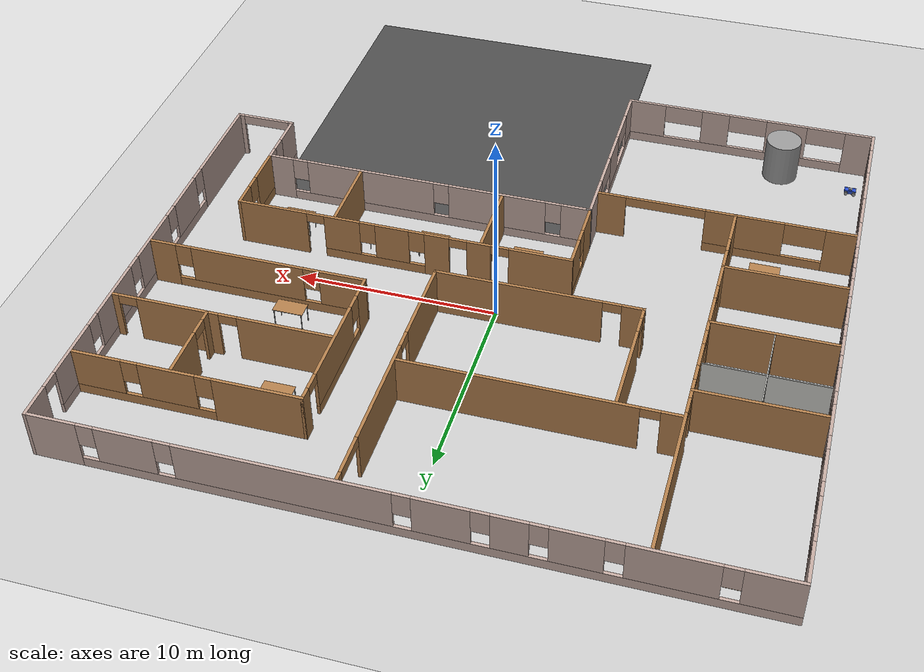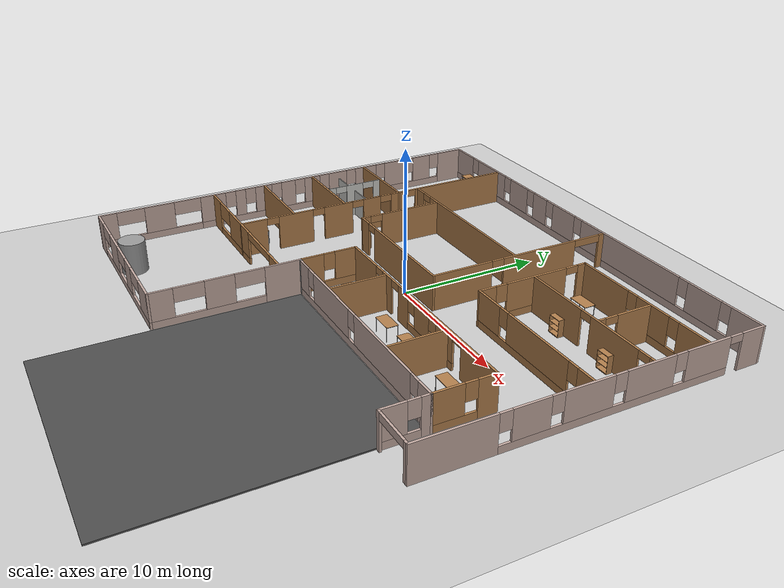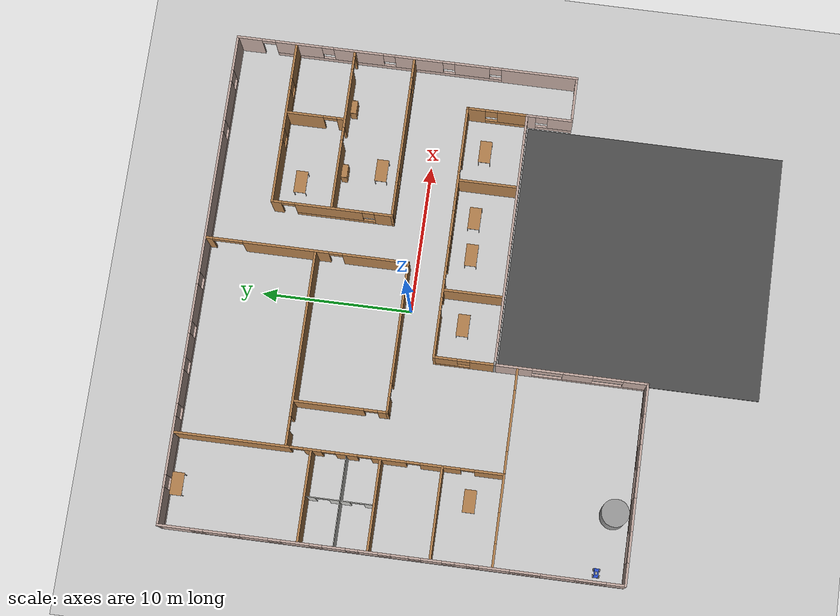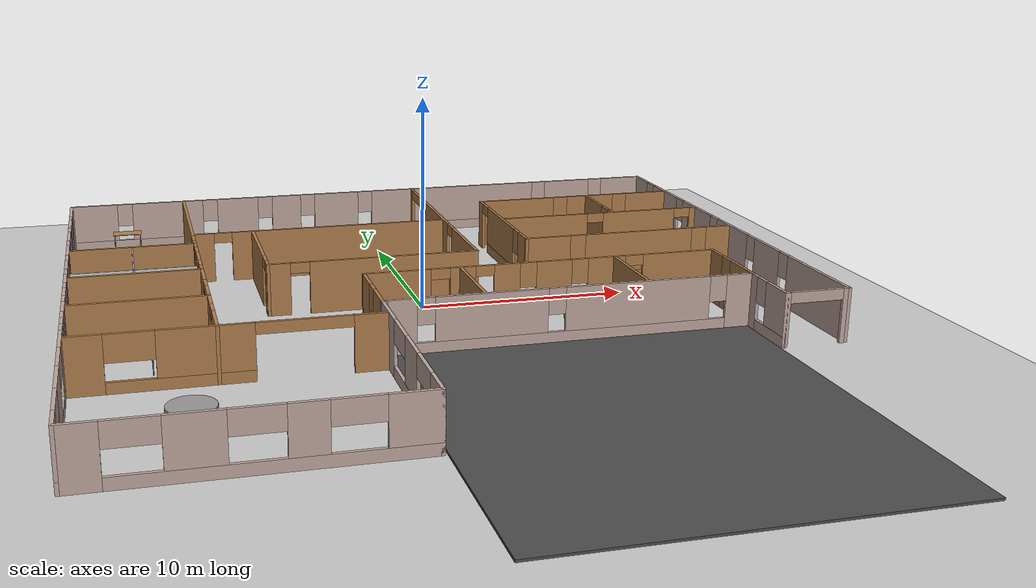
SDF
<sdf version="1.7">
 <world name="default">
  <light name="sun" type="directional">
   <pose>0 0 10 0 -0 0</pose>
   <diffuse>0.8 0.8 0.8 1</diffuse>
   <specular>0.2 0.2 0.2 1</specular>
   <attenuation>
    <range>1000</range>
    <constant>0.9</constant>
    <linear>0.01</linear>
    <quadratic>0.001</quadratic>
   </attenuation>
   <direction>-0.5 0.1 -0.9</direction>
   <spot><inner_angle>0</inner_angle><outer_angle>0</outer_angle><falloff>0</falloff></spot>
  </light>
  <model name="ground_plane">
   <static>1</static>
   <link name="link">
    <collision name="collision">
     <geometry><plane><normal>0 0 1</normal><size>100 100</size></plane></geometry>
     <surface>
      <contact><collide_bitmask>65535</collide_bitmask></contact>
      <friction><ode><mu>100</mu><mu2>50</mu2></ode></friction>
     </surface>
    </collision>
    <visual name="visual">
     <cast_shadows>0</cast_shadows>
     <geometry><plane><normal>0 0 1</normal><size>100 100</size></plane></geometry>
     <material>
      <script><uri>file://media/materials/scripts/gazebo.material</uri><name>Gazebo/Grey</name></script>
     </material>
    </visual>
   </link>
  </model>
  <gravity>0 0 -9.8</gravity>
  <magnetic_field>6e-06 2.3e-05 -4.2e-05</magnetic_field>
  <atmosphere type="adiabatic"/>
  <physics type="ode">
   <max_step_size>0.001</max_step_size>
   <real_time_factor>1</real_time_factor>
   <real_time_update_rate>1000</real_time_update_rate>
  </physics>
  <scene><ambient>0.4 0.4 0.4 1</ambient><background>0.7 0.7 0.7 1</background><shadows>1</shadows></scene>
  <spherical_coordinates>
   <surface_model>EARTH_WGS84</surface_model>
   <latitude_deg>0</latitude_deg>
   <longitude_deg>0</longitude_deg>
   <elevation>0</elevation>
   <heading_deg>0</heading_deg>
  </spherical_coordinates>
  <model name="Office">
   <pose>0.30406 -0.9941 0 0 -0 0</pose>
   <link name="Wall_0">
    <pose>-10 -15 0 0 -0 0</pose>
    <visual name="Wall_0_Visual_0">
     <pose>-5.81535 0 1.25 0 -0 0</pose>
     <geometry><box><size>1.51931 0.15 2.5</size></box></geometry>
     <material>
      <script><uri>file://media/materials/scripts/gazebo.material</uri><name>Gazebo/Grey</name></script>
      <ambient>0.760784 0.662745 0.627451 1</ambient>
     </material>
     <meta><layer>0</layer></meta>
    </visual>
    <collision name="Wall_0_Collision_0">
     <geometry><box><size>1.51931 0.15 2.5</size></box></geometry>
     <pose>-5.81535 0 1.25 0 -0 0</pose>
    </collision>
    <visual name="Wall_0_Visual_1">
     <pose>0.759654 0 0.25 0 -0 0</pose>
     <geometry><box><size>11.6307 0.15 0.5</size></box></geometry>
     <material>
      <script><uri>file://media/materials/scripts/gazebo.material</uri><name>Gazebo/Grey</name></script>
      <ambient>0.760784 0.662745 0.627451 1</ambient>
     </material>
     <meta><layer>0</layer></meta>
    </visual>
    <collision name="Wall_0_Collision_1">
     <geometry><box><size>11.6307 0.15 0.5</size></box></geometry>
     <pose>0.759654 0 0.25 0 -0 0</pose>
    </collision>
    <visual name="Wall_0_Visual_2">
     <pose>-1.98547 0 1.5 0 -0 0</pose>
     <geometry><box><size>2.14044 0.15 2</size></box></geometry>
     <material>
      <script><uri>file://media/materials/scripts/gazebo.material</uri><name>Gazebo/Grey</name></script>
      <ambient>0.760784 0.662745 0.627451 1</ambient>
     </material>
     <meta><layer>0</layer></meta>
    </visual>
    <collision name="Wall_0_Collision_2">
     <geometry><box><size>2.14044 0.15 2</size></box></geometry>
     <pose>-1.98547 0 1.5 0 -0 0</pose>
    </collision>
    <visual name="Wall_0_Visual_3">
     <pose>1.82008 0 1.5 0 -0 0</pose>
     <geometry><box><size>1.47066 0.15 2</size></box></geometry>
     <material>
      <script><uri>file://media/materials/scripts/gazebo.material</uri><name>Gazebo/Grey</name></script>
      <ambient>0.760784 0.662745 0.627451 1</ambient>
     </material>
     <meta><layer>0</layer></meta>
    </visual>
    <collision name="Wall_0_Collision_3">
     <geometry><box><size>1.47066 0.15 2</size></box></geometry>
     <pose>1.82008 0 1.5 0 -0 0</pose>
    </collision>
    <visual name="Wall_0_Visual_4">
     <pose>5.56521 0 1.5 0 -0 0</pose>
     <geometry><box><size>2.01958 0.15 2</size></box></geometry>
     <material>
      <script><uri>file://media/materials/scripts/gazebo.material</uri><name>Gazebo/Grey</name></script>
      <ambient>0.760784 0.662745 0.627451 1</ambient>
     </material>
     <meta><layer>0</layer></meta>
    </visual>
    <collision name="Wall_0_Collision_4">
     <geometry><box><size>2.01958 0.15 2</size></box></geometry>
     <pose>5.56521 0 1.5 0 -0 0</pose>
    </collision>
    <visual name="Wall_0_Visual_5">
     <pose>-4.05569 0 2 0 -0 0</pose>
     <geometry><box><size>2 0.15 1</size></box></geometry>
     <material>
      <script><uri>file://media/materials/scripts/gazebo.material</uri><name>Gazebo/Grey</name></script>
      <ambient>0.760784 0.662745 0.627451 1</ambient>
     </material>
     <meta><layer>0</layer></meta>
    </visual>
    <collision name="Wall_0_Collision_5">
     <geometry><box><size>2 0.15 1</size></box></geometry>
     <pose>-4.05569 0 2 0 -0 0</pose>
    </collision>
    <visual name="Wall_0_Visual_6">
     <pose>0.084752 0 2 0 -0 0</pose>
     <geometry><box><size>2 0.15 1</size></box></geometry>
     <material>
      <script><uri>file://media/materials/scripts/gazebo.material</uri><name>Gazebo/Grey</name></script>
      <ambient>0.760784 0.662745 0.627451 1</ambient>
     </material>
     <meta><layer>0</layer></meta>
    </visual>
    <collision name="Wall_0_Collision_6">
     <geometry><box><size>2 0.15 1</size></box></geometry>
     <pose>0.084752 0 2 0 -0 0</pose>
    </collision>
    <visual name="Wall_0_Visual_7">
     <pose>3.55542 0 2 0 -0 0</pose>
     <geometry><box><size>2 0.15 1</size></box></geometry>
     <material>
      <script><uri>file://media/materials/scripts/gazebo.material</uri><name>Gazebo/Grey</name></script>
      <ambient>0.760784 0.662745 0.627451 1</ambient>
     </material>
     <meta><layer>0</layer></meta>
    </visual>
    <collision name="Wall_0_Collision_7">
     <geometry><box><size>2 0.15 1</size></box></geometry>
     <pose>3.55542 0 2 0 -0 0</pose>
    </collision>
   </link>
   <link name="Wall_12">
    <pose>-10.5 4.175 0 0 -0 1.5708</pose>
    <visual name="Wall_12_Visual_0">
     <pose>-9.76618 0 1.25 0 -0 0</pose>
     <geometry><box><size>1.96818 0.15 2.5</size></box></geometry>
     <material>
      <script><uri>file://media/materials/scripts/gazebo.material</uri><name>Gazebo/Wood</name></script>
      <ambient>1 1 1 1</ambient>
     </material>
     <meta><layer>0</layer></meta>
    </visual>
    <collision name="Wall_12_Collision_0">
     <geometry><box><size>1.96818 0.15 2.5</size></box></geometry>
     <pose>-9.76618 0 1.25 0 -0 0</pose>
    </collision>
    <visual name="Wall_12_Visual_1">
     <pose>-6.55733 0 1.25 0 -0 0</pose>
     <geometry><box><size>2.64952 0.15 2.5</size></box></geometry>
     <material>
      <script><uri>file://media/materials/scripts/gazebo.material</uri><name>Gazebo/Wood</name></script>
      <ambient>1 1 1 1</ambient>
     </material>
     <meta><layer>0</layer></meta>
    </visual>
    <collision name="Wall_12_Collision_1">
     <geometry><box><size>2.64952 0.15 2.5</size></box></geometry>
     <pose>-6.55733 0 1.25 0 -0 0</pose>
    </collision>
    <visual name="Wall_12_Visual_2">
     <pose>-3.19706 0 1.25 0 -0 0</pose>
     <geometry><box><size>2.27101 0.15 2.5</size></box></geometry>
     <material>
      <script><uri>file://media/materials/scripts/gazebo.material</uri><name>Gazebo/Wood</name></script>
      <ambient>1 1 1 1</ambient>
     </material>
     <meta><layer>0</layer></meta>
    </visual>
    <collision name="Wall_12_Collision_2">
     <geometry><box><size>2.27101 0.15 2.5</size></box></geometry>
     <pose>-3.19706 0 1.25 0 -0 0</pose>
    </collision>
    <visual name="Wall_12_Visual_3">
     <pose>-0.451144 0 1.25 0 -0 0</pose>
     <geometry><box><size>1.42083 0.15 2.5</size></box></geometry>
     <material>
      <script><uri>file://media/materials/scripts/gazebo.material</uri><name>Gazebo/Wood</name></script>
      <ambient>1 1 1 1</ambient>
     </material>
     <meta><layer>0</layer></meta>
    </visual>
    <collision name="Wall_12_Collision_3">
     <geometry><box><size>1.42083 0.15 2.5</size></box></geometry>
     <pose>-0.451144 0 1.25 0 -0 0</pose>
    </collision>
    <visual name="Wall_12_Visual_4">
     <pose>1.7422 0 1.25 0 -0 0</pose>
     <geometry><box><size>1.16586 0.15 2.5</size></box></geometry>
     <material>
      <script><uri>file://media/materials/scripts/gazebo.material</uri><name>Gazebo/Wood</name></script>
      <ambient>1 1 1 1</ambient>
     </material>
     <meta><layer>0</layer></meta>
    </visual>
    <collision name="Wall_12_Collision_4">
     <geometry><box><size>1.16586 0.15 2.5</size></box></geometry>
     <pose>1.7422 0 1.25 0 -0 0</pose>
    </collision>
    <visual name="Wall_12_Visual_5">
     <pose>6.9877 0 1.25 0 -0 0</pose>
     <geometry><box><size>7.52514 0.15 2.5</size></box></geometry>
     <material>
      <script><uri>file://media/materials/scripts/gazebo.material</uri><name>Gazebo/Wood</name></script>
      <ambient>1 1 1 1</ambient>
     </material>
     <meta><layer>0</layer></meta>
    </visual>
    <collision name="Wall_12_Collision_5">
     <geometry><box><size>7.52514 0.15 2.5</size></box></geometry>
     <pose>6.9877 0 1.25 0 -0 0</pose>
    </collision>
    <visual name="Wall_12_Visual_6">
     <pose>-8.33209 0 2.25 0 -0 0</pose>
     <geometry><box><size>0.9 0.15 0.5</size></box></geometry>
     <material>
      <script><uri>file://media/materials/scripts/gazebo.material</uri><name>Gazebo/Wood</name></script>
      <ambient>1 1 1 1</ambient>
     </material>
     <meta><layer>0</layer></meta>
    </visual>
    <collision name="Wall_12_Collision_6">
     <geometry><box><size>0.9 0.15 0.5</size></box></geometry>
     <pose>-8.33209 0 2.25 0 -0 0</pose>
    </collision>
    <visual name="Wall_12_Visual_7">
     <pose>-4.78257 0 2.25 0 -0 0</pose>
     <geometry><box><size>0.9 0.15 0.5</size></box></geometry>
     <material>
      <script><uri>file://media/materials/scripts/gazebo.material</uri><name>Gazebo/Wood</name></script>
      <ambient>1 1 1 1</ambient>
     </material>
     <meta><layer>0</layer></meta>
    </visual>
    <collision name="Wall_12_Collision_7">
     <geometry><box><size>0.9 0.15 0.5</size></box></geometry>
     <pose>-4.78257 0 2.25 0 -0 0</pose>
    </collision>
    <visual name="Wall_12_Visual_8">
     <pose>-1.61156 0 2.25 0 -0 0</pose>
     <geometry><box><size>0.9 0.15 0.5</size></box></geometry>
     <material>
      <script><uri>file://media/materials/scripts/gazebo.material</uri><name>Gazebo/Wood</name></script>
      <ambient>1 1 1 1</ambient>
     </material>
     <meta><layer>0</layer></meta>
    </visual>
    <collision name="Wall_12_Collision_8">
     <geometry><box><size>0.9 0.15 0.5</size></box></geometry>
     <pose>-1.61156 0 2.25 0 -0 0</pose>
    </collision>
    <visual name="Wall_12_Visual_9">
     <pose>0.709272 0 2.25 0 -0 0</pose>
     <geometry><box><size>0.9 0.15 0.5</size></box></geometry>
     <material>
      <script><uri>file://media/materials/scripts/gazebo.material</uri><name>Gazebo/Wood</name></script>
      <ambient>1 1 1 1</ambient>
     </material>
     <meta><layer>0</layer></meta>
    </visual>
    <collision name="Wall_12_Collision_9">
     <geometry><box><size>0.9 0.15 0.5</size></box></geometry>
     <pose>0.709272 0 2.25 0 -0 0</pose>
    </collision>
    <visual name="Wall_12_Visual_10">
     <pose>2.77513 0 2.25 0 -0 0</pose>
     <geometry><box><size>0.9 0.15 0.5</size></box></geometry>
     <material>
      <script><uri>file://media/materials/scripts/gazebo.material</uri><name>Gazebo/Wood</name></script>
      <ambient>1 1 1 1</ambient>
     </material>
     <meta><layer>0</layer></meta>
    </visual>
    <collision name="Wall_12_Collision_10">
     <geometry><box><size>0.9 0.15 0.5</size></box></geometry>
     <pose>2.77513 0 2.25 0 -0 0</pose>
    </collision>
   </link>
   <link name="Wall_22">
    <pose>5 -5 0 0 -0 3.14159</pose>
    <visual name="Wall_22_Visual_0">
     <pose>-7.90117 0 1.25 0 -0 0</pose>
     <geometry><box><size>1.34767 0.15 2.5</size></box></geometry>
     <material>
      <script><uri>file://media/materials/scripts/gazebo.material</uri><name>Gazebo/Grey</name></script>
      <ambient>0.760784 0.662745 0.627451 1</ambient>
     </material>
     <meta><layer>0</layer></meta>
    </visual>
    <collision name="Wall_22_Collision_0">
     <geometry><box><size>1.34767 0.15 2.5</size></box></geometry>
     <pose>-7.90117 0 1.25 0 -0 0</pose>
    </collision>
    <visual name="Wall_22_Visual_1">
     <pose>0.673833 0 0.25 0 -0 0</pose>
     <geometry><box><size>15.8023 0.15 0.5</size></box></geometry>
     <material>
      <script><uri>file://media/materials/scripts/gazebo.material</uri><name>Gazebo/Grey</name></script>
      <ambient>0.760784 0.662745 0.627451 1</ambient>
     </material>
     <meta><layer>0</layer></meta>
    </visual>
    <collision name="Wall_22_Collision_1">
     <geometry><box><size>15.8023 0.15 0.5</size></box></geometry>
     <pose>0.673833 0 0.25 0 -0 0</pose>
    </collision>
    <visual name="Wall_22_Visual_2">
     <pose>-3.02957 0 1.5 0 -0 0</pose>
     <geometry><box><size>6.79553 0.15 2</size></box></geometry>
     <material>
      <script><uri>file://media/materials/scripts/gazebo.material</uri><name>Gazebo/Grey</name></script>
      <ambient>0.760784 0.662745 0.627451 1</ambient>
     </material>
     <meta><layer>0</layer></meta>
    </visual>
    <collision name="Wall_22_Collision_2">
     <geometry><box><size>6.79553 0.15 2</size></box></geometry>
     <pose>-3.02957 0 1.5 0 -0 0</pose>
    </collision>
    <visual name="Wall_22_Visual_3">
     <pose>3.69491 0 1.5 0 -0 0</pose>
     <geometry><box><size>5.05343 0.15 2</size></box></geometry>
     <material>
      <script><uri>file://media/materials/scripts/gazebo.material</uri><name>Gazebo/Grey</name></script>
      <ambient>0.760784 0.662745 0.627451 1</ambient>
     </material>
     <meta><layer>0</layer></meta>
    </visual>
    <collision name="Wall_22_Collision_3">
     <geometry><box><size>5.05343 0.15 2</size></box></geometry>
     <pose>3.69491 0 1.5 0 -0 0</pose>
    </collision>
    <visual name="Wall_22_Visual_4">
     <pose>7.79831 0 1.5 0 -0 0</pose>
     <geometry><box><size>1.55337 0.15 2</size></box></geometry>
     <material>
      <script><uri>file://media/materials/scripts/gazebo.material</uri><name>Gazebo/Grey</name></script>
      <ambient>0.760784 0.662745 0.627451 1</ambient>
     </material>
     <meta><layer>0</layer></meta>
    </visual>
    <collision name="Wall_22_Collision_4">
     <geometry><box><size>1.55337 0.15 2</size></box></geometry>
     <pose>7.79831 0 1.5 0 -0 0</pose>
    </collision>
    <visual name="Wall_22_Visual_5">
     <pose>-6.82733 0 1.9 0 -0 0</pose>
     <geometry><box><size>0.8 0.15 1.2</size></box></geometry>
     <material>
      <script><uri>file://media/materials/scripts/gazebo.material</uri><name>Gazebo/Grey</name></script>
      <ambient>0.760784 0.662745 0.627451 1</ambient>
     </material>
     <meta><layer>0</layer></meta>
    </visual>
    <collision name="Wall_22_Collision_5">
     <geometry><box><size>0.8 0.15 1.2</size></box></geometry>
     <pose>-6.82733 0 1.9 0 -0 0</pose>
    </collision>
    <visual name="Wall_22_Visual_6">
     <pose>0.768194 0 1.9 0 -0 0</pose>
     <geometry><box><size>0.8 0.15 1.2</size></box></geometry>
     <material>
      <script><uri>file://media/materials/scripts/gazebo.material</uri><name>Gazebo/Grey</name></script>
      <ambient>0.760784 0.662745 0.627451 1</ambient>
     </material>
     <meta><layer>0</layer></meta>
    </visual>
    <collision name="Wall_22_Collision_6">
     <geometry><box><size>0.8 0.15 1.2</size></box></geometry>
     <pose>0.768194 0 1.9 0 -0 0</pose>
    </collision>
    <visual name="Wall_22_Visual_7">
     <pose>6.62163 0 1.9 0 -0 0</pose>
     <geometry><box><size>0.8 0.15 1.2</size></box></geometry>
     <material>
      <script><uri>file://media/materials/scripts/gazebo.material</uri><name>Gazebo/Grey</name></script>
      <ambient>0.760784 0.662745 0.627451 1</ambient>
     </material>
     <meta><layer>0</layer></meta>
    </visual>
    <collision name="Wall_22_Collision_7">
     <geometry><box><size>0.8 0.15 1.2</size></box></geometry>
     <pose>6.62163 0 1.9 0 -0 0</pose>
    </collision>
   </link>
   <link name="Wall_24">
    <collision name="Wall_24_Collision">
     <geometry><box><size>3.85 0.15 2.5</size></box></geometry>
     <pose>0 0 1.25 0 -0 0</pose>
    </collision>
    <visual name="Wall_24_Visual">
     <pose>0 0 1.25 0 -0 0</pose>
     <geometry><box><size>3.85 0.15 2.5</size></box></geometry>
     <material>
      <script><uri>file://media/materials/scripts/gazebo.material</uri><name>Gazebo/Wood</name></script>
      <ambient>1 1 1 1</ambient>
     </material>
     <meta><layer>0</layer></meta>
    </visual>
    <pose>8.5 -3 0 0 -0 -1.5708</pose>
   </link>
   <link name="Wall_26">
    <collision name="Wall_26_Collision">
     <geometry><box><size>3.85 0.15 2.5</size></box></geometry>
     <pose>0 0 1.25 0 -0 0</pose>
    </collision>
    <visual name="Wall_26_Visual">
     <pose>0 0 1.25 0 -0 0</pose>
     <geometry><box><size>3.85 0.15 2.5</size></box></geometry>
     <material>
      <script><uri>file://media/materials/scripts/gazebo.material</uri><name>Gazebo/Wood</name></script>
      <ambient>1 1 1 1</ambient>
     </material>
     <meta><layer>0</layer></meta>
    </visual>
    <pose>1 -3 0 0 -0 -1.5708</pose>
   </link>
   <link name="Wall_28">
    <pose>10.925 3 0 0 -0 3.14159</pose>
    <visual name="Wall_28_Visual_0">
     <pose>-4.84691 0 1.25 0 -0 0</pose>
     <geometry><box><size>1.30617 0.15 2.5</size></box></geometry>
     <material>
      <script><uri>file://media/materials/scripts/gazebo.material</uri><name>Gazebo/Wood</name></script>
      <ambient>1 1 1 1</ambient>
     </material>
     <meta><layer>0</layer></meta>
    </visual>
    <collision name="Wall_28_Collision_0">
     <geometry><box><size>1.30617 0.15 2.5</size></box></geometry>
     <pose>-4.84691 0 1.25 0 -0 0</pose>
    </collision>
    <visual name="Wall_28_Visual_1">
     <pose>0.653086 0 0.25 0 -0 0</pose>
     <geometry><box><size>9.69383 0.15 0.5</size></box></geometry>
     <material>
      <script><uri>file://media/materials/scripts/gazebo.material</uri><name>Gazebo/Wood</name></script>
      <ambient>1 1 1 1</ambient>
     </material>
     <meta><layer>0</layer></meta>
    </visual>
    <collision name="Wall_28_Collision_1">
     <geometry><box><size>9.69383 0.15 0.5</size></box></geometry>
     <pose>0.653086 0 0.25 0 -0 0</pose>
    </collision>
    <visual name="Wall_28_Visual_2">
     <pose>-0.525148 0 1.5 0 -0 0</pose>
     <geometry><box><size>5.73736 0.15 2</size></box></geometry>
     <material>
      <script><uri>file://media/materials/scripts/gazebo.material</uri><name>Gazebo/Wood</name></script>
      <ambient>1 1 1 1</ambient>
     </material>
     <meta><layer>0</layer></meta>
    </visual>
    <collision name="Wall_28_Collision_2">
     <geometry><box><size>5.73736 0.15 2</size></box></geometry>
     <pose>-0.525148 0 1.5 0 -0 0</pose>
    </collision>
    <visual name="Wall_28_Visual_3">
     <pose>4.32177 0 1.5 0 -0 0</pose>
     <geometry><box><size>2.35647 0.15 2</size></box></geometry>
     <material>
      <script><uri>file://media/materials/scripts/gazebo.material</uri><name>Gazebo/Wood</name></script>
      <ambient>1 1 1 1</ambient>
     </material>
     <meta><layer>0</layer></meta>
    </visual>
    <collision name="Wall_28_Collision_3">
     <geometry><box><size>2.35647 0.15 2</size></box></geometry>
     <pose>4.32177 0 1.5 0 -0 0</pose>
    </collision>
    <visual name="Wall_28_Visual_4">
     <pose>-3.79383 0 1.9 0 -0 0</pose>
     <geometry><box><size>0.8 0.15 1.2</size></box></geometry>
     <material>
      <script><uri>file://media/materials/scripts/gazebo.material</uri><name>Gazebo/Wood</name></script>
      <ambient>1 1 1 1</ambient>
     </material>
     <meta><layer>0</layer></meta>
    </visual>
    <collision name="Wall_28_Collision_4">
     <geometry><box><size>0.8 0.15 1.2</size></box></geometry>
     <pose>-3.79383 0 1.9 0 -0 0</pose>
    </collision>
    <visual name="Wall_28_Visual_5">
     <pose>2.74353 0 1.9 0 -0 0</pose>
     <geometry><box><size>0.8 0.15 1.2</size></box></geometry>
     <material>
      <script><uri>file://media/materials/scripts/gazebo.material</uri><name>Gazebo/Wood</name></script>
      <ambient>1 1 1 1</ambient>
     </material>
     <meta><layer>0</layer></meta>
    </visual>
    <collision name="Wall_28_Collision_5">
     <geometry><box><size>0.8 0.15 1.2</size></box></geometry>
     <pose>2.74353 0 1.9 0 -0 0</pose>
    </collision>
   </link>
   <link name="Wall_29">
    <pose>5.5 7 0 0 -0 1.5708</pose>
    <visual name="Wall_29_Visual_0">
     <pose>-3.44549 0 1.25 0 -0 0</pose>
     <geometry><box><size>1.25902 0.15 2.5</size></box></geometry>
     <material>
      <script><uri>file://media/materials/scripts/gazebo.material</uri><name>Gazebo/Wood</name></script>
      <ambient>1 1 1 1</ambient>
     </material>
     <meta><layer>0</layer></meta>
    </visual>
    <collision name="Wall_29_Collision_0">
     <geometry><box><size>1.25902 0.15 2.5</size></box></geometry>
     <pose>-3.44549 0 1.25 0 -0 0</pose>
    </collision>
    <visual name="Wall_29_Visual_1">
     <pose>3.72696 0 1.25 0 -0 0</pose>
     <geometry><box><size>0.696084 0.15 2.5</size></box></geometry>
     <material>
      <script><uri>file://media/materials/scripts/gazebo.material</uri><name>Gazebo/Wood</name></script>
      <ambient>1 1 1 1</ambient>
     </material>
     <meta><layer>0</layer></meta>
    </visual>
    <collision name="Wall_29_Collision_1">
     <geometry><box><size>0.696084 0.15 2.5</size></box></geometry>
     <pose>3.72696 0 1.25 0 -0 0</pose>
    </collision>
    <visual name="Wall_29_Visual_2">
     <pose>-0.168534 0 0.25 0 -0 0</pose>
     <geometry><box><size>5.2949 0.15 0.5</size></box></geometry>
     <material>
      <script><uri>file://media/materials/scripts/gazebo.material</uri><name>Gazebo/Wood</name></script>
      <ambient>1 1 1 1</ambient>
     </material>
     <meta><layer>0</layer></meta>
    </visual>
    <collision name="Wall_29_Collision_2">
     <geometry><box><size>5.2949 0.15 0.5</size></box></geometry>
     <pose>-0.168534 0 0.25 0 -0 0</pose>
    </collision>
    <visual name="Wall_29_Visual_3">
     <pose>0.231466 0 1.5 0 -0 0</pose>
     <geometry><box><size>4.4949 0.15 2</size></box></geometry>
     <material>
      <script><uri>file://media/materials/scripts/gazebo.material</uri><name>Gazebo/Wood</name></script>
      <ambient>1 1 1 1</ambient>
     </material>
     <meta><layer>0</layer></meta>
    </visual>
    <collision name="Wall_29_Collision_3">
     <geometry><box><size>4.4949 0.15 2</size></box></geometry>
     <pose>0.231466 0 1.5 0 -0 0</pose>
    </collision>
    <visual name="Wall_29_Visual_4">
     <pose>-2.41598 0 1.9 0 -0 0</pose>
     <geometry><box><size>0.8 0.15 1.2</size></box></geometry>
     <material>
      <script><uri>file://media/materials/scripts/gazebo.material</uri><name>Gazebo/Wood</name></script>
      <ambient>1 1 1 1</ambient>
     </material>
     <meta><layer>0</layer></meta>
    </visual>
    <collision name="Wall_29_Collision_4">
     <geometry><box><size>0.8 0.15 1.2</size></box></geometry>
     <pose>-2.41598 0 1.9 0 -0 0</pose>
    </collision>
    <visual name="Wall_29_Visual_5">
     <pose>2.92892 0 2.25 0 -0 0</pose>
     <geometry><box><size>0.9 0.15 0.5</size></box></geometry>
     <material>
      <script><uri>file://media/materials/scripts/gazebo.material</uri><name>Gazebo/Wood</name></script>
      <ambient>1 1 1 1</ambient>
     </material>
     <meta><layer>0</layer></meta>
    </visual>
    <collision name="Wall_29_Collision_5">
     <geometry><box><size>0.9 0.15 0.5</size></box></geometry>
     <pose>2.92892 0 2.25 0 -0 0</pose>
    </collision>
   </link>
   <link name="Wall_3">
    <pose>16.5 3.5 0 0 -0 1.5708</pose>
    <visual name="Wall_3_Visual_0">
     <pose>-8.99285 0 1.25 0 -0 0</pose>
     <geometry><box><size>5.16431 0.15 2.5</size></box></geometry>
     <material>
      <script><uri>file://media/materials/scripts/gazebo.material</uri><name>Gazebo/Grey</name></script>
      <ambient>0.760784 0.662745 0.627451 1</ambient>
     </material>
     <meta><layer>0</layer></meta>
    </visual>
    <collision name="Wall_3_Collision_0">
     <geometry><box><size>5.16431 0.15 2.5</size></box></geometry>
     <pose>-8.99285 0 1.25 0 -0 0</pose>
    </collision>
    <visual name="Wall_3_Visual_1">
     <pose>10.7143 0 1.25 0 -0 0</pose>
     <geometry><box><size>1.72148 0.15 2.5</size></box></geometry>
     <material>
      <script><uri>file://media/materials/scripts/gazebo.material</uri><name>Gazebo/Grey</name></script>
      <ambient>0.760784 0.662745 0.627451 1</ambient>
     </material>
     <meta><layer>0</layer></meta>
    </visual>
    <collision name="Wall_3_Collision_1">
     <geometry><box><size>1.72148 0.15 2.5</size></box></geometry>
     <pose>10.7143 0 1.25 0 -0 0</pose>
    </collision>
    <visual name="Wall_3_Visual_2">
     <pose>1.27141 0 0.25 0 -0 0</pose>
     <geometry><box><size>15.3642 0.15 0.5</size></box></geometry>
     <material>
      <script><uri>file://media/materials/scripts/gazebo.material</uri><name>Gazebo/Grey</name></script>
      <ambient>0.760784 0.662745 0.627451 1</ambient>
     </material>
     <meta><layer>0</layer></meta>
    </visual>
    <collision name="Wall_3_Collision_2">
     <geometry><box><size>15.3642 0.15 0.5</size></box></geometry>
     <pose>1.27141 0 0.25 0 -0 0</pose>
    </collision>
    <visual name="Wall_3_Visual_3">
     <pose>-4.42189 0 1.5 0 -0 0</pose>
     <geometry><box><size>2.3776 0.15 2</size></box></geometry>
     <material>
      <script><uri>file://media/materials/scripts/gazebo.material</uri><name>Gazebo/Grey</name></script>
      <ambient>0.760784 0.662745 0.627451 1</ambient>
     </material>
     <meta><layer>0</layer></meta>
    </visual>
    <collision name="Wall_3_Collision_3">
     <geometry><box><size>2.3776 0.15 2</size></box></geometry>
     <pose>-4.42189 0 1.5 0 -0 0</pose>
    </collision>
    <visual name="Wall_3_Visual_4">
     <pose>-0.80608 0 1.5 0 -0 0</pose>
     <geometry><box><size>3.25401 0.15 2</size></box></geometry>
     <material>
      <script><uri>file://media/materials/scripts/gazebo.material</uri><name>Gazebo/Grey</name></script>
      <ambient>0.760784 0.662745 0.627451 1</ambient>
     </material>
     <meta><layer>0</layer></meta>
    </visual>
    <collision name="Wall_3_Collision_4">
     <geometry><box><size>3.25401 0.15 2</size></box></geometry>
     <pose>-0.80608 0 1.5 0 -0 0</pose>
    </collision>
    <visual name="Wall_3_Visual_5">
     <pose>3.30392 0 1.5 0 -0 0</pose>
     <geometry><box><size>3.36599 0.15 2</size></box></geometry>
     <material>
      <script><uri>file://media/materials/scripts/gazebo.material</uri><name>Gazebo/Grey</name></script>
      <ambient>0.760784 0.662745 0.627451 1</ambient>
     </material>
     <meta><layer>0</layer></meta>
    </visual>
    <collision name="Wall_3_Collision_5">
     <geometry><box><size>3.36599 0.15 2</size></box></geometry>
     <pose>3.30392 0 1.5 0 -0 0</pose>
    </collision>
    <visual name="Wall_3_Visual_6">
     <pose>7.37022 0 1.5 0 -0 0</pose>
     <geometry><box><size>3.1666 0.15 2</size></box></geometry>
     <material>
      <script><uri>file://media/materials/scripts/gazebo.material</uri><name>Gazebo/Grey</name></script>
      <ambient>0.760784 0.662745 0.627451 1</ambient>
     </material>
     <meta><layer>0</layer></meta>
    </visual>
    <collision name="Wall_3_Collision_6">
     <geometry><box><size>3.1666 0.15 2</size></box></geometry>
     <pose>7.37022 0 1.5 0 -0 0</pose>
    </collision>
    <visual name="Wall_3_Visual_7">
     <pose>-6.01069 0 1.9 0 -0 0</pose>
     <geometry><box><size>0.8 0.15 1.2</size></box></geometry>
     <material>
      <script><uri>file://media/materials/scripts/gazebo.material</uri><name>Gazebo/Grey</name></script>
      <ambient>0.760784 0.662745 0.627451 1</ambient>
     </material>
     <meta><layer>0</layer></meta>
    </visual>
    <collision name="Wall_3_Collision_7">
     <geometry><box><size>0.8 0.15 1.2</size></box></geometry>
     <pose>-6.01069 0 1.9 0 -0 0</pose>
    </collision>
    <visual name="Wall_3_Visual_8">
     <pose>-2.83308 0 1.9 0 -0 0</pose>
     <geometry><box><size>0.8 0.15 1.2</size></box></geometry>
     <material>
      <script><uri>file://media/materials/scripts/gazebo.material</uri><name>Gazebo/Grey</name></script>
      <ambient>0.760784 0.662745 0.627451 1</ambient>
     </material>
     <meta><layer>0</layer></meta>
    </visual>
    <collision name="Wall_3_Collision_8">
     <geometry><box><size>0.8 0.15 1.2</size></box></geometry>
     <pose>-2.83308 0 1.9 0 -0 0</pose>
    </collision>
    <visual name="Wall_3_Visual_9">
     <pose>1.22093 0 1.9 0 -0 0</pose>
     <geometry><box><size>0.8 0.15 1.2</size></box></geometry>
     <material>
      <script><uri>file://media/materials/scripts/gazebo.material</uri><name>Gazebo/Grey</name></script>
      <ambient>0.760784 0.662745 0.627451 1</ambient>
     </material>
     <meta><layer>0</layer></meta>
    </visual>
    <collision name="Wall_3_Collision_9">
     <geometry><box><size>0.8 0.15 1.2</size></box></geometry>
     <pose>1.22093 0 1.9 0 -0 0</pose>
    </collision>
    <visual name="Wall_3_Visual_10">
     <pose>5.38691 0 1.9 0 -0 0</pose>
     <geometry><box><size>0.8 0.15 1.2</size></box></geometry>
     <material>
      <script><uri>file://media/materials/scripts/gazebo.material</uri><name>Gazebo/Grey</name></script>
      <ambient>0.760784 0.662745 0.627451 1</ambient>
     </material>
     <meta><layer>0</layer></meta>
    </visual>
    <collision name="Wall_3_Collision_10">
     <geometry><box><size>0.8 0.15 1.2</size></box></geometry>
     <pose>5.38691 0 1.9 0 -0 0</pose>
    </collision>
    <visual name="Wall_3_Visual_11">
     <pose>9.40352 0 2.25 0 -0 0</pose>
     <geometry><box><size>0.9 0.15 0.5</size></box></geometry>
     <material>
      <script><uri>file://media/materials/scripts/gazebo.material</uri><name>Gazebo/Grey</name></script>
      <ambient>0.760784 0.662745 0.627451 1</ambient>
     </material>
     <meta><layer>0</layer></meta>
    </visual>
    <collision name="Wall_3_Collision_11">
     <geometry><box><size>0.9 0.15 0.5</size></box></geometry>
     <pose>9.40352 0 2.25 0 -0 0</pose>
    </collision>
   </link>
   <link name="Wall_30">
    <pose>10.925 11 0 0 -0 0</pose>
    <visual name="Wall_30_Visual_0">
     <pose>-3.35391 0 1.25 0 -0 0</pose>
     <geometry><box><size>4.29219 0.15 2.5</size></box></geometry>
     <material>
      <script><uri>file://media/materials/scripts/gazebo.material</uri><name>Gazebo/Wood</name></script>
      <ambient>1 1 1 1</ambient>
     </material>
     <meta><layer>0</layer></meta>
    </visual>
    <collision name="Wall_30_Collision_0">
     <geometry><box><size>4.29219 0.15 2.5</size></box></geometry>
     <pose>-3.35391 0 1.25 0 -0 0</pose>
    </collision>
    <visual name="Wall_30_Visual_1">
     <pose>2.1461 0 0.25 0 -0 0</pose>
     <geometry><box><size>6.70781 0.15 0.5</size></box></geometry>
     <material>
      <script><uri>file://media/materials/scripts/gazebo.material</uri><name>Gazebo/Wood</name></script>
      <ambient>1 1 1 1</ambient>
     </material>
     <meta><layer>0</layer></meta>
    </visual>
    <collision name="Wall_30_Collision_1">
     <geometry><box><size>6.70781 0.15 0.5</size></box></geometry>
     <pose>2.1461 0 0.25 0 -0 0</pose>
    </collision>
    <visual name="Wall_30_Visual_2">
     <pose>0.957967 0 1.5 0 -0 0</pose>
     <geometry><box><size>2.73155 0.15 2</size></box></geometry>
     <material>
      <script><uri>file://media/materials/scripts/gazebo.material</uri><name>Gazebo/Wood</name></script>
      <ambient>1 1 1 1</ambient>
     </material>
     <meta><layer>0</layer></meta>
    </visual>
    <collision name="Wall_30_Collision_2">
     <geometry><box><size>2.73155 0.15 2</size></box></geometry>
     <pose>0.957967 0 1.5 0 -0 0</pose>
    </collision>
    <visual name="Wall_30_Visual_3">
     <pose>4.31187 0 1.5 0 -0 0</pose>
     <geometry><box><size>2.37626 0.15 2</size></box></geometry>
     <material>
      <script><uri>file://media/materials/scripts/gazebo.material</uri><name>Gazebo/Wood</name></script>
      <ambient>1 1 1 1</ambient>
     </material>
     <meta><layer>0</layer></meta>
    </visual>
    <collision name="Wall_30_Collision_3">
     <geometry><box><size>2.37626 0.15 2</size></box></geometry>
     <pose>4.31187 0 1.5 0 -0 0</pose>
    </collision>
    <visual name="Wall_30_Visual_4">
     <pose>-0.80781 0 1.9 0 -0 0</pose>
     <geometry><box><size>0.8 0.15 1.2</size></box></geometry>
     <material>
      <script><uri>file://media/materials/scripts/gazebo.material</uri><name>Gazebo/Wood</name></script>
      <ambient>1 1 1 1</ambient>
     </material>
     <meta><layer>0</layer></meta>
    </visual>
    <collision name="Wall_30_Collision_4">
     <geometry><box><size>0.8 0.15 1.2</size></box></geometry>
     <pose>-0.80781 0 1.9 0 -0 0</pose>
    </collision>
    <visual name="Wall_30_Visual_5">
     <pose>2.72374 0 1.9 0 -0 0</pose>
     <geometry><box><size>0.8 0.15 1.2</size></box></geometry>
     <material>
      <script><uri>file://media/materials/scripts/gazebo.material</uri><name>Gazebo/Wood</name></script>
      <ambient>1 1 1 1</ambient>
     </material>
     <meta><layer>0</layer></meta>
    </visual>
    <collision name="Wall_30_Collision_5">
     <geometry><box><size>0.8 0.15 1.2</size></box></geometry>
     <pose>2.72374 0 1.9 0 -0 0</pose>
    </collision>
   </link>
   <link name="Wall_32">
    <pose>2.5 8.175 0 0 -0 -1.5708</pose>
    <visual name="Wall_32_Visual_0">
     <pose>-6.5375 0 1.25 0 -0 0</pose>
     <geometry><box><size>0.425 0.15 2.5</size></box></geometry>
     <material>
      <script><uri>file://media/materials/scripts/gazebo.material</uri><name>Gazebo/Wood</name></script>
      <ambient>1 1 1 1</ambient>
     </material>
     <meta><layer>0</layer></meta>
    </visual>
    <collision name="Wall_32_Collision_0">
     <geometry><box><size>0.425 0.15 2.5</size></box></geometry>
     <pose>-6.5375 0 1.25 0 -0 0</pose>
    </collision>
    <visual name="Wall_32_Visual_1">
     <pose>-1.45325 0 1.25 0 -0 0</pose>
     <geometry><box><size>5.7435 0.15 2.5</size></box></geometry>
     <material>
      <script><uri>file://media/materials/scripts/gazebo.material</uri><name>Gazebo/Wood</name></script>
      <ambient>1 1 1 1</ambient>
     </material>
     <meta><layer>0</layer></meta>
    </visual>
    <collision name="Wall_32_Collision_1">
     <geometry><box><size>5.7435 0.15 2.5</size></box></geometry>
     <pose>-1.45325 0 1.25 0 -0 0</pose>
    </collision>
    <visual name="Wall_32_Visual_2">
     <pose>4.53425 0 1.25 0 -0 0</pose>
     <geometry><box><size>4.4315 0.15 2.5</size></box></geometry>
     <material>
      <script><uri>file://media/materials/scripts/gazebo.material</uri><name>Gazebo/Wood</name></script>
      <ambient>1 1 1 1</ambient>
     </material>
     <meta><layer>0</layer></meta>
    </visual>
    <collision name="Wall_32_Collision_2">
     <geometry><box><size>4.4315 0.15 2.5</size></box></geometry>
     <pose>4.53425 0 1.25 0 -0 0</pose>
    </collision>
    <visual name="Wall_32_Visual_3">
     <pose>-5.325 0 2.25 0 -0 0</pose>
     <geometry><box><size>2 0.15 0.5</size></box></geometry>
     <material>
      <script><uri>file://media/materials/scripts/gazebo.material</uri><name>Gazebo/Wood</name></script>
      <ambient>1 1 1 1</ambient>
     </material>
     <meta><layer>0</layer></meta>
    </visual>
    <collision name="Wall_32_Collision_3">
     <geometry><box><size>2 0.15 0.5</size></box></geometry>
     <pose>-5.325 0 2.25 0 -0 0</pose>
    </collision>
    <visual name="Wall_32_Visual_4">
     <pose>1.8685 0 2.25 0 -0 0</pose>
     <geometry><box><size>0.9 0.15 0.5</size></box></geometry>
     <material>
      <script><uri>file://media/materials/scripts/gazebo.material</uri><name>Gazebo/Wood</name></script>
      <ambient>1 1 1 1</ambient>
     </material>
     <meta><layer>0</layer></meta>
    </visual>
    <collision name="Wall_32_Collision_4">
     <geometry><box><size>0.9 0.15 0.5</size></box></geometry>
     <pose>1.8685 0 2.25 0 -0 0</pose>
    </collision>
   </link>
   <link name="Wall_33">
    <pose>-2.5 1.5 0 0 -0 3.14159</pose>
    <visual name="Wall_33_Visual_0">
     <pose>-1.0046 0 1.25 0 -0 0</pose>
     <geometry><box><size>8.1408 0.15 2.5</size></box></geometry>
     <material>
      <script><uri>file://media/materials/scripts/gazebo.material</uri><name>Gazebo/Wood</name></script>
      <ambient>1 1 1 1</ambient>
     </material>
     <meta><layer>0</layer></meta>
    </visual>
    <collision name="Wall_33_Collision_0">
     <geometry><box><size>8.1408 0.15 2.5</size></box></geometry>
     <pose>-1.0046 0 1.25 0 -0 0</pose>
    </collision>
    <visual name="Wall_33_Visual_1">
     <pose>4.5204 0 1.25 0 -0 0</pose>
     <geometry><box><size>1.1092 0.15 2.5</size></box></geometry>
     <material>
      <script><uri>file://media/materials/scripts/gazebo.material</uri><name>Gazebo/Wood</name></script>
      <ambient>1 1 1 1</ambient>
     </material>
     <meta><layer>0</layer></meta>
    </visual>
    <collision name="Wall_33_Collision_1">
     <geometry><box><size>1.1092 0.15 2.5</size></box></geometry>
     <pose>4.5204 0 1.25 0 -0 0</pose>
    </collision>
    <visual name="Wall_33_Visual_2">
     <pose>3.5158 0 2.25 0 -0 0</pose>
     <geometry><box><size>0.9 0.15 0.5</size></box></geometry>
     <material>
      <script><uri>file://media/materials/scripts/gazebo.material</uri><name>Gazebo/Wood</name></script>
      <ambient>1 1 1 1</ambient>
     </material>
     <meta><layer>0</layer></meta>
    </visual>
    <collision name="Wall_33_Collision_2">
     <geometry><box><size>0.9 0.15 0.5</size></box></geometry>
     <pose>3.5158 0 2.25 0 -0 0</pose>
    </collision>
   </link>
   <link name="Wall_34">
    <pose>-7.5 4.5 0 0 -0 1.5708</pose>
    <visual name="Wall_34_Visual_0">
     <pose>-2.73019 0 1.25 0 -0 0</pose>
     <geometry><box><size>0.689623 0.15 2.5</size></box></geometry>
     <material>
      <script><uri>file://media/materials/scripts/gazebo.material</uri><name>Gazebo/Wood</name></script>
      <ambient>1 1 1 1</ambient>
     </material>
     <meta><layer>0</layer></meta>
    </visual>
    <collision name="Wall_34_Collision_0">
     <geometry><box><size>0.689623 0.15 2.5</size></box></geometry>
     <pose>-2.73019 0 1.25 0 -0 0</pose>
    </collision>
    <visual name="Wall_34_Visual_1">
     <pose>0.794812 0 1.25 0 -0 0</pose>
     <geometry><box><size>4.56038 0.15 2.5</size></box></geometry>
     <material>
      <script><uri>file://media/materials/scripts/gazebo.material</uri><name>Gazebo/Wood</name></script>
      <ambient>1 1 1 1</ambient>
     </material>
     <meta><layer>0</layer></meta>
    </visual>
    <collision name="Wall_34_Collision_1">
     <geometry><box><size>4.56038 0.15 2.5</size></box></geometry>
     <pose>0.794812 0 1.25 0 -0 0</pose>
    </collision>
    <visual name="Wall_34_Visual_2">
     <pose>-1.93538 0 2.25 0 -0 0</pose>
     <geometry><box><size>0.9 0.15 0.5</size></box></geometry>
     <material>
      <script><uri>file://media/materials/scripts/gazebo.material</uri><name>Gazebo/Wood</name></script>
      <ambient>1 1 1 1</ambient>
     </material>
     <meta><layer>0</layer></meta>
    </visual>
    <collision name="Wall_34_Collision_2">
     <geometry><box><size>0.9 0.15 0.5</size></box></geometry>
     <pose>-1.93538 0 2.25 0 -0 0</pose>
    </collision>
   </link>
   <link name="Wall_36">
    <pose>-4 7.65 0 0 -0 0</pose>
    <visual name="Wall_36_Visual_0">
     <pose>-5.93774 0 1.25 0 -0 0</pose>
     <geometry><box><size>0.974511 0.15 2.5</size></box></geometry>
     <material>
      <script><uri>file://media/materials/scripts/gazebo.material</uri><name>Gazebo/Wood</name></script>
      <ambient>1 1 1 1</ambient>
     </material>
     <meta><layer>0</layer></meta>
    </visual>
    <collision name="Wall_36_Collision_0">
     <geometry><box><size>0.974511 0.15 2.5</size></box></geometry>
     <pose>-5.93774 0 1.25 0 -0 0</pose>
    </collision>
    <visual name="Wall_36_Visual_1">
     <pose>0.937255 0 1.25 0 -0 0</pose>
     <geometry><box><size>10.9755 0.15 2.5</size></box></geometry>
     <material>
      <script><uri>file://media/materials/scripts/gazebo.material</uri><name>Gazebo/Wood</name></script>
      <ambient>1 1 1 1</ambient>
     </material>
     <meta><layer>0</layer></meta>
    </visual>
    <collision name="Wall_36_Collision_1">
     <geometry><box><size>10.9755 0.15 2.5</size></box></geometry>
     <pose>0.937255 0 1.25 0 -0 0</pose>
    </collision>
    <visual name="Wall_36_Visual_2">
     <pose>-5.00049 0 2.25 0 -0 0</pose>
     <geometry><box><size>0.9 0.15 0.5</size></box></geometry>
     <material>
      <script><uri>file://media/materials/scripts/gazebo.material</uri><name>Gazebo/Wood</name></script>
      <ambient>1 1 1 1</ambient>
     </material>
     <meta><layer>0</layer></meta>
    </visual>
    <collision name="Wall_36_Collision_2">
     <geometry><box><size>0.9 0.15 0.5</size></box></geometry>
     <pose>-5.00049 0 2.25 0 -0 0</pose>
    </collision>
   </link>
   <link name="Wall_38">
    <collision name="Wall_38_Collision">
     <geometry><box><size>6 0.15 2.5</size></box></geometry>
     <pose>0 0 1.25 0 -0 0</pose>
    </collision>
    <visual name="Wall_38_Visual">
     <pose>0 0 1.25 0 -0 0</pose>
     <geometry><box><size>6 0.15 2.5</size></box></geometry>
     <material>
      <script><uri>file://media/materials/scripts/gazebo.material</uri><name>Gazebo/Wood</name></script>
      <ambient>1 1 1 1</ambient>
     </material>
     <meta><layer>0</layer></meta>
    </visual>
    <pose>-13.425 6 0 0 -0 3.14159</pose>
   </link>
   <link name="Wall_4">
    <pose>0 15 0 0 -0 3.14159</pose>
    <visual name="Wall_4_Visual_0">
     <pose>-15.3518 0 1.25 0 -0 0</pose>
     <geometry><box><size>2.44634 0.15 2.5</size></box></geometry>
     <material>
      <script><uri>file://media/materials/scripts/gazebo.material</uri><name>Gazebo/Grey</name></script>
      <ambient>0.760784 0.662745 0.627451 1</ambient>
     </material>
     <meta><layer>0</layer></meta>
    </visual>
    <collision name="Wall_4_Collision_0">
     <geometry><box><size>2.44634 0.15 2.5</size></box></geometry>
     <pose>-15.3518 0 1.25 0 -0 0</pose>
    </collision>
    <visual name="Wall_4_Visual_1">
     <pose>1.22317 0 0.25 0 -0 0</pose>
     <geometry><box><size>30.7037 0.15 0.5</size></box></geometry>
     <material>
      <script><uri>file://media/materials/scripts/gazebo.material</uri><name>Gazebo/Grey</name></script>
      <ambient>0.760784 0.662745 0.627451 1</ambient>
     </material>
     <meta><layer>0</layer></meta>
    </visual>
    <collision name="Wall_4_Collision_1">
     <geometry><box><size>30.7037 0.15 0.5</size></box></geometry>
     <pose>1.22317 0 0.25 0 -0 0</pose>
    </collision>
    <visual name="Wall_4_Visual_2">
     <pose>-11.9571 0 1.5 0 -0 0</pose>
     <geometry><box><size>2.74312 0.15 2</size></box></geometry>
     <material>
      <script><uri>file://media/materials/scripts/gazebo.material</uri><name>Gazebo/Grey</name></script>
      <ambient>0.760784 0.662745 0.627451 1</ambient>
     </material>
     <meta><layer>0</layer></meta>
    </visual>
    <collision name="Wall_4_Collision_2">
     <geometry><box><size>2.74312 0.15 2</size></box></geometry>
     <pose>-11.9571 0 1.5 0 -0 0</pose>
    </collision>
    <visual name="Wall_4_Visual_3">
     <pose>-4.95138 0 1.5 0 -0 0</pose>
     <geometry><box><size>9.66832 0.15 2</size></box></geometry>
     <material>
      <script><uri>file://media/materials/scripts/gazebo.material</uri><name>Gazebo/Grey</name></script>
      <ambient>0.760784 0.662745 0.627451 1</ambient>
     </material>
     <meta><layer>0</layer></meta>
    </visual>
    <collision name="Wall_4_Collision_3">
     <geometry><box><size>9.66832 0.15 2</size></box></geometry>
     <pose>-4.95138 0 1.5 0 -0 0</pose>
    </collision>
    <visual name="Wall_4_Visual_4">
     <pose>1.93356 0 1.5 0 -0 0</pose>
     <geometry><box><size>2.50155 0.15 2</size></box></geometry>
     <material>
      <script><uri>file://media/materials/scripts/gazebo.material</uri><name>Gazebo/Grey</name></script>
      <ambient>0.760784 0.662745 0.627451 1</ambient>
     </material>
     <meta><layer>0</layer></meta>
    </visual>
    <collision name="Wall_4_Collision_4">
     <geometry><box><size>2.50155 0.15 2</size></box></geometry>
     <pose>1.93356 0 1.5 0 -0 0</pose>
    </collision>
    <visual name="Wall_4_Visual_5">
     <pose>4.79221 0 1.5 0 -0 0</pose>
     <geometry><box><size>1.61577 0.15 2</size></box></geometry>
     <material>
      <script><uri>file://media/materials/scripts/gazebo.material</uri><name>Gazebo/Grey</name></script>
      <ambient>0.760784 0.662745 0.627451 1</ambient>
     </material>
     <meta><layer>0</layer></meta>
    </visual>
    <collision name="Wall_4_Collision_5">
     <geometry><box><size>1.61577 0.15 2</size></box></geometry>
     <pose>4.79221 0 1.5 0 -0 0</pose>
    </collision>
    <visual name="Wall_4_Visual_6">
     <pose>7.53008 0 1.5 0 -0 0</pose>
     <geometry><box><size>2.25997 0.15 2</size></box></geometry>
     <material>
      <script><uri>file://media/materials/scripts/gazebo.material</uri><name>Gazebo/Grey</name></script>
      <ambient>0.760784 0.662745 0.627451 1</ambient>
     </material>
     <meta><layer>0</layer></meta>
    </visual>
    <collision name="Wall_4_Collision_6">
     <geometry><box><size>2.25997 0.15 2</size></box></geometry>
     <pose>7.53008 0 1.5 0 -0 0</pose>
    </collision>
    <visual name="Wall_4_Visual_7">
     <pose>11.3752 0 1.5 0 -0 0</pose>
     <geometry><box><size>3.83029 0.15 2</size></box></geometry>
     <material>
      <script><uri>file://media/materials/scripts/gazebo.material</uri><name>Gazebo/Grey</name></script>
      <ambient>0.760784 0.662745 0.627451 1</ambient>
     </material>
     <meta><layer>0</layer></meta>
    </visual>
    <collision name="Wall_4_Collision_7">
     <geometry><box><size>3.83029 0.15 2</size></box></geometry>
     <pose>11.3752 0 1.5 0 -0 0</pose>
    </collision>
    <visual name="Wall_4_Visual_8">
     <pose>15.3327 0 1.5 0 -0 0</pose>
     <geometry><box><size>2.48464 0.15 2</size></box></geometry>
     <material>
      <script><uri>file://media/materials/scripts/gazebo.material</uri><name>Gazebo/Grey</name></script>
      <ambient>0.760784 0.662745 0.627451 1</ambient>
     </material>
     <meta><layer>0</layer></meta>
    </visual>
    <collision name="Wall_4_Collision_8">
     <geometry><box><size>2.48464 0.15 2</size></box></geometry>
     <pose>15.3327 0 1.5 0 -0 0</pose>
    </collision>
    <visual name="Wall_4_Visual_9">
     <pose>-13.7287 0 1.9 0 -0 0</pose>
     <geometry><box><size>0.8 0.15 1.2</size></box></geometry>
     <material>
      <script><uri>file://media/materials/scripts/gazebo.material</uri><name>Gazebo/Grey</name></script>
      <ambient>0.760784 0.662745 0.627451 1</ambient>
     </material>
     <meta><layer>0</layer></meta>
    </visual>
    <collision name="Wall_4_Collision_9">
     <geometry><box><size>0.8 0.15 1.2</size></box></geometry>
     <pose>-13.7287 0 1.9 0 -0 0</pose>
    </collision>
    <visual name="Wall_4_Visual_10">
     <pose>-10.1855 0 1.9 0 -0 0</pose>
     <geometry><box><size>0.8 0.15 1.2</size></box></geometry>
     <material>
      <script><uri>file://media/materials/scripts/gazebo.material</uri><name>Gazebo/Grey</name></script>
      <ambient>0.760784 0.662745 0.627451 1</ambient>
     </material>
     <meta><layer>0</layer></meta>
    </visual>
    <collision name="Wall_4_Collision_10">
     <geometry><box><size>0.8 0.15 1.2</size></box></geometry>
     <pose>-10.1855 0 1.9 0 -0 0</pose>
    </collision>
    <visual name="Wall_4_Visual_11">
     <pose>0.282784 0 1.9 0 -0 0</pose>
     <geometry><box><size>0.8 0.15 1.2</size></box></geometry>
     <material>
      <script><uri>file://media/materials/scripts/gazebo.material</uri><name>Gazebo/Grey</name></script>
      <ambient>0.760784 0.662745 0.627451 1</ambient>
     </material>
     <meta><layer>0</layer></meta>
    </visual>
    <collision name="Wall_4_Collision_11">
     <geometry><box><size>0.8 0.15 1.2</size></box></geometry>
     <pose>0.282784 0 1.9 0 -0 0</pose>
    </collision>
    <visual name="Wall_4_Visual_12">
     <pose>3.58433 0 1.9 0 -0 0</pose>
     <geometry><box><size>0.8 0.15 1.2</size></box></geometry>
     <material>
      <script><uri>file://media/materials/scripts/gazebo.material</uri><name>Gazebo/Grey</name></script>
      <ambient>0.760784 0.662745 0.627451 1</ambient>
     </material>
     <meta><layer>0</layer></meta>
    </visual>
    <collision name="Wall_4_Collision_12">
     <geometry><box><size>0.8 0.15 1.2</size></box></geometry>
     <pose>3.58433 0 1.9 0 -0 0</pose>
    </collision>
    <visual name="Wall_4_Visual_13">
     <pose>6.0001 0 1.9 0 -0 0</pose>
     <geometry><box><size>0.8 0.15 1.2</size></box></geometry>
     <material>
      <script><uri>file://media/materials/scripts/gazebo.material</uri><name>Gazebo/Grey</name></script>
      <ambient>0.760784 0.662745 0.627451 1</ambient>
     </material>
     <meta><layer>0</layer></meta>
    </visual>
    <collision name="Wall_4_Collision_13">
     <geometry><box><size>0.8 0.15 1.2</size></box></geometry>
     <pose>6.0001 0 1.9 0 -0 0</pose>
    </collision>
    <visual name="Wall_4_Visual_14">
     <pose>9.06007 0 1.9 0 -0 0</pose>
     <geometry><box><size>0.8 0.15 1.2</size></box></geometry>
     <material>
      <script><uri>file://media/materials/scripts/gazebo.material</uri><name>Gazebo/Grey</name></script>
      <ambient>0.760784 0.662745 0.627451 1</ambient>
     </material>
     <meta><layer>0</layer></meta>
    </visual>
    <collision name="Wall_4_Collision_14">
     <geometry><box><size>0.8 0.15 1.2</size></box></geometry>
     <pose>9.06007 0 1.9 0 -0 0</pose>
    </collision>
    <visual name="Wall_4_Visual_15">
     <pose>13.6904 0 1.9 0 -0 0</pose>
     <geometry><box><size>0.8 0.15 1.2</size></box></geometry>
     <material>
      <script><uri>file://media/materials/scripts/gazebo.material</uri><name>Gazebo/Grey</name></script>
      <ambient>0.760784 0.662745 0.627451 1</ambient>
     </material>
     <meta><layer>0</layer></meta>
    </visual>
    <collision name="Wall_4_Collision_15">
     <geometry><box><size>0.8 0.15 1.2</size></box></geometry>
     <pose>13.6904 0 1.9 0 -0 0</pose>
    </collision>
   </link>
   <link name="Wall_41">
    <collision name="Wall_41_Collision">
     <geometry><box><size>6 0.15 2.5</size></box></geometry>
     <pose>0 0 1.25 0 -0 0</pose>
    </collision>
    <visual name="Wall_41_Visual">
     <pose>0 0 1.25 0 -0 0</pose>
     <geometry><box><size>6 0.15 2.5</size></box></geometry>
     <material>
      <script><uri>file://media/materials/scripts/gazebo.material</uri><name>Gazebo/Wood</name></script>
      <ambient>1 1 1 1</ambient>
     </material>
     <meta><layer>0</layer></meta>
    </visual>
    <pose>-13.425 1.5 0 0 -0 0</pose>
   </link>
   <link name="Wall_43">
    <collision name="Wall_43_Collision">
     <geometry><box><size>6 0.15 2.5</size></box></geometry>
     <pose>0 0 1.25 0 -0 0</pose>
    </collision>
    <visual name="Wall_43_Visual">
     <pose>0 0 1.25 0 -0 0</pose>
     <geometry><box><size>6 0.15 2.5</size></box></geometry>
     <material>
      <script><uri>file://media/materials/scripts/gazebo.material</uri><name>Gazebo/Wood</name></script>
      <ambient>1 1 1 1</ambient>
     </material>
     <meta><layer>0</layer></meta>
    </visual>
    <pose>-13.425 -2.5 0 0 -0 0</pose>
   </link>
   <link name="Wall_45">
    <collision name="Wall_45_Collision">
     <geometry><box><size>5.9 0.05 2</size></box></geometry>
     <pose>0 0 1 0 -0 0</pose>
    </collision>
    <visual name="Wall_45_Visual">
     <pose>0 0 1 0 -0 0</pose>
     <geometry><box><size>5.9 0.05 2</size></box></geometry>
     <material>
      <script><uri>file://media/materials/scripts/gazebo.material</uri><name>Gazebo/CeilingTiled</name></script>
      <ambient>1 1 1 1</ambient>
     </material>
     <meta><layer>0</layer></meta>
    </visual>
    <pose>-13.425 3.75 0 0 -0 3.14159</pose>
   </link>
   <link name="Wall_47">
    <pose>-13.5 3.75 0 0 -0 -1.5708</pose>
    <visual name="Wall_47_Visual_0">
     <pose>-1.85464 0 1.25 0 -0 0</pose>
     <geometry><box><size>0.540727 0.05 2.5</size></box></geometry>
     <material>
      <script><uri>file://media/materials/scripts/gazebo.material</uri><name>Gazebo/CeilingTiled</name></script>
      <ambient>1 1 1 1</ambient>
     </material>
     <meta><layer>0</layer></meta>
    </visual>
    <collision name="Wall_47_Collision_0">
     <geometry><box><size>0.540727 0.05 2.5</size></box></geometry>
     <pose>-1.85464 0 1.25 0 -0 0</pose>
    </collision>
    <visual name="Wall_47_Visual_1">
     <pose>-0.00216 0 1.25 0 -0 0</pose>
     <geometry><box><size>1.36423 0.05 2.5</size></box></geometry>
     <material>
      <script><uri>file://media/materials/scripts/gazebo.material</uri><name>Gazebo/CeilingTiled</name></script>
      <ambient>1 1 1 1</ambient>
     </material>
     <meta><layer>0</layer></meta>
    </visual>
    <collision name="Wall_47_Collision_1">
     <geometry><box><size>1.36423 0.05 2.5</size></box></geometry>
     <pose>-0.00216 0 1.25 0 -0 0</pose>
    </collision>
    <visual name="Wall_47_Visual_2">
     <pose>1.85248 0 1.25 0 -0 0</pose>
     <geometry><box><size>0.545047 0.05 2.5</size></box></geometry>
     <material>
      <script><uri>file://media/materials/scripts/gazebo.material</uri><name>Gazebo/CeilingTiled</name></script>
      <ambient>1 1 1 1</ambient>
     </material>
     <meta><layer>0</layer></meta>
    </visual>
    <collision name="Wall_47_Collision_2">
     <geometry><box><size>0.545047 0.05 2.5</size></box></geometry>
     <pose>1.85248 0 1.25 0 -0 0</pose>
    </collision>
    <visual name="Wall_47_Visual_3">
     <pose>-1.13427 0 2.25 0 -0 0</pose>
     <geometry><box><size>0.9 0.05 0.5</size></box></geometry>
     <material>
      <script><uri>file://media/materials/scripts/gazebo.material</uri><name>Gazebo/CeilingTiled</name></script>
      <ambient>1 1 1 1</ambient>
     </material>
     <meta><layer>0</layer></meta>
    </visual>
    <collision name="Wall_47_Collision_3">
     <geometry><box><size>0.9 0.05 0.5</size></box></geometry>
     <pose>-1.13427 0 2.25 0 -0 0</pose>
    </collision>
    <visual name="Wall_47_Visual_4">
     <pose>1.12995 0 2.25 0 -0 0</pose>
     <geometry><box><size>0.9 0.05 0.5</size></box></geometry>
     <material>
      <script><uri>file://media/materials/scripts/gazebo.material</uri><name>Gazebo/CeilingTiled</name></script>
      <ambient>1 1 1 1</ambient>
     </material>
     <meta><layer>0</layer></meta>
    </visual>
    <collision name="Wall_47_Collision_4">
     <geometry><box><size>0.9 0.05 0.5</size></box></geometry>
     <pose>1.12995 0 2.25 0 -0 0</pose>
    </collision>
   </link>
   <link name="Wall_49">
    <pose>-10 -6.5 0 0 -0 0</pose>
    <visual name="Wall_49_Visual_0">
     <pose>-5.674 0 1.25 0 -0 0</pose>
     <geometry><box><size>1.502 0.15 2.5</size></box></geometry>
     <material>
      <script><uri>file://media/materials/scripts/gazebo.material</uri><name>Gazebo/Wood</name></script>
      <ambient>1 1 1 1</ambient>
     </material>
     <meta><layer>0</layer></meta>
    </visual>
    <collision name="Wall_49_Collision_0">
     <geometry><box><size>1.502 0.15 2.5</size></box></geometry>
     <pose>-5.674 0 1.25 0 -0 0</pose>
    </collision>
    <visual name="Wall_49_Visual_1">
     <pose>5.7125 0 1.25 0 -0 0</pose>
     <geometry><box><size>1.425 0.15 2.5</size></box></geometry>
     <material>
      <script><uri>file://media/materials/scripts/gazebo.material</uri><name>Gazebo/Wood</name></script>
      <ambient>1 1 1 1</ambient>
     </material>
     <meta><layer>0</layer></meta>
    </visual>
    <collision name="Wall_49_Collision_1">
     <geometry><box><size>1.425 0.15 2.5</size></box></geometry>
     <pose>5.7125 0 1.25 0 -0 0</pose>
    </collision>
    <visual name="Wall_49_Visual_2">
     <pose>-1.9615 0 0.25 0 -0 0</pose>
     <geometry><box><size>5.923 0.15 0.5</size></box></geometry>
     <material>
      <script><uri>file://media/materials/scripts/gazebo.material</uri><name>Gazebo/Wood</name></script>
      <ambient>1 1 1 1</ambient>
     </material>
     <meta><layer>0</layer></meta>
    </visual>
    <collision name="Wall_49_Collision_2">
     <geometry><box><size>5.923 0.15 0.5</size></box></geometry>
     <pose>-1.9615 0 0.25 0 -0 0</pose>
    </collision>
    <visual name="Wall_49_Visual_3">
     <pose>-0.9615 0 1.5 0 -0 0</pose>
     <geometry><box><size>3.923 0.15 2</size></box></geometry>
     <material>
      <script><uri>file://media/materials/scripts/gazebo.material</uri><name>Gazebo/Wood</name></script>
      <ambient>1 1 1 1</ambient>
     </material>
     <meta><layer>0</layer></meta>
    </visual>
    <collision name="Wall_49_Collision_3">
     <geometry><box><size>3.923 0.15 2</size></box></geometry>
     <pose>-0.9615 0 1.5 0 -0 0</pose>
    </collision>
    <visual name="Wall_49_Visual_4">
     <pose>-3.923 0 1.9 0 -0 0</pose>
     <geometry><box><size>2 0.15 1.2</size></box></geometry>
     <material>
      <script><uri>file://media/materials/scripts/gazebo.material</uri><name>Gazebo/Wood</name></script>
      <ambient>1 1 1 1</ambient>
     </material>
     <meta><layer>0</layer></meta>
    </visual>
    <collision name="Wall_49_Collision_4">
     <geometry><box><size>2 0.15 1.2</size></box></geometry>
     <pose>-3.923 0 1.9 0 -0 0</pose>
    </collision>
    <visual name="Wall_49_Visual_5">
     <pose>3 0 2.25 0 -0 0</pose>
     <geometry><box><size>4 0.15 0.5</size></box></geometry>
     <material>
      <script><uri>file://media/materials/scripts/gazebo.material</uri><name>Gazebo/Wood</name></script>
      <ambient>1 1 1 1</ambient>
     </material>
     <meta><layer>0</layer></meta>
    </visual>
    <collision name="Wall_49_Collision_5">
     <geometry><box><size>4 0.15 0.5</size></box></geometry>
     <pose>3 0 2.25 0 -0 0</pose>
    </collision>
   </link>
   <link name="Wall_5">
    <pose>-16.5 0 0 0 -0 -1.5708</pose>
    <visual name="Wall_5_Visual_0">
     <pose>-13.9772 0 1.25 0 -0 0</pose>
     <geometry><box><size>2.19564 0.15 2.5</size></box></geometry>
     <material>
      <script><uri>file://media/materials/scripts/gazebo.material</uri><name>Gazebo/Grey</name></script>
      <ambient>0.760784 0.662745 0.627451 1</ambient>
     </material>
     <meta><layer>0</layer></meta>
    </visual>
    <collision name="Wall_5_Collision_0">
     <geometry><box><size>2.19564 0.15 2.5</size></box></geometry>
     <pose>-13.9772 0 1.25 0 -0 0</pose>
    </collision>
    <visual name="Wall_5_Visual_1">
     <pose>-2.64558 0 0.25 0 -0 0</pose>
     <geometry><box><size>20.4675 0.15 0.5</size></box></geometry>
     <material>
      <script><uri>file://media/materials/scripts/gazebo.material</uri><name>Gazebo/Grey</name></script>
      <ambient>0.760784 0.662745 0.627451 1</ambient>
     </material>
     <meta><layer>0</layer></meta>
    </visual>
    <collision name="Wall_5_Collision_1">
     <geometry><box><size>20.4675 0.15 0.5</size></box></geometry>
     <pose>-2.64558 0 0.25 0 -0 0</pose>
    </collision>
    <visual name="Wall_5_Visual_2">
     <pose>11.3316 0 0.25 0 -0 0</pose>
     <geometry><box><size>7.48681 0.15 0.5</size></box></geometry>
     <material>
      <script><uri>file://media/materials/scripts/gazebo.material</uri><name>Gazebo/Grey</name></script>
      <ambient>0.760784 0.662745 0.627451 1</ambient>
     </material>
     <meta><layer>0</layer></meta>
    </visual>
    <collision name="Wall_5_Collision_2">
     <geometry><box><size>7.48681 0.15 0.5</size></box></geometry>
     <pose>11.3316 0 0.25 0 -0 0</pose>
    </collision>
    <visual name="Wall_5_Visual_3">
     <pose>10.6889 0 1.5 0 -0 0</pose>
     <geometry><box><size>2.20133 0.15 2</size></box></geometry>
     <material>
      <script><uri>file://media/materials/scripts/gazebo.material</uri><name>Gazebo/Grey</name></script>
      <ambient>0.760784 0.662745 0.627451 1</ambient>
     </material>
     <meta><layer>0</layer></meta>
    </visual>
    <collision name="Wall_5_Collision_3">
     <geometry><box><size>2.20133 0.15 2</size></box></geometry>
     <pose>10.6889 0 1.5 0 -0 0</pose>
    </collision>
    <visual name="Wall_5_Visual_4">
     <pose>14.4323 0 1.5 0 -0 0</pose>
     <geometry><box><size>1.28547 0.15 2</size></box></geometry>
     <material>
      <script><uri>file://media/materials/scripts/gazebo.material</uri><name>Gazebo/Grey</name></script>
      <ambient>0.760784 0.662745 0.627451 1</ambient>
     </material>
     <meta><layer>0</layer></meta>
    </visual>
    <collision name="Wall_5_Collision_4">
     <geometry><box><size>1.28547 0.15 2</size></box></geometry>
     <pose>14.4323 0 1.5 0 -0 0</pose>
    </collision>
    <visual name="Wall_5_Visual_5">
     <pose>-11.292 0 1.5 0 -0 0</pose>
     <geometry><box><size>1.57467 0.15 2</size></box></geometry>
     <material>
      <script><uri>file://media/materials/scripts/gazebo.material</uri><name>Gazebo/Grey</name></script>
      <ambient>0.760784 0.662745 0.627451 1</ambient>
     </material>
     <meta><layer>0</layer></meta>
    </visual>
    <collision name="Wall_5_Collision_5">
     <geometry><box><size>1.57467 0.15 2</size></box></geometry>
     <pose>-11.292 0 1.5 0 -0 0</pose>
    </collision>
    <visual name="Wall_5_Visual_6">
     <pose>-8.79558 0 1.5 0 -0 0</pose>
     <geometry><box><size>1.81822 0.15 2</size></box></geometry>
     <material>
      <script><uri>file://media/materials/scripts/gazebo.material</uri><name>Gazebo/Grey</name></script>
      <ambient>0.760784 0.662745 0.627451 1</ambient>
     </material>
     <meta><layer>0</layer></meta>
    </visual>
    <collision name="Wall_5_Collision_6">
     <geometry><box><size>1.81822 0.15 2</size></box></geometry>
     <pose>-8.79558 0 1.5 0 -0 0</pose>
    </collision>
    <visual name="Wall_5_Visual_7">
     <pose>-6.15707 0 1.5 0 -0 0</pose>
     <geometry><box><size>1.8588 0.15 2</size></box></geometry>
     <material>
      <script><uri>file://media/materials/scripts/gazebo.material</uri><name>Gazebo/Grey</name></script>
      <ambient>0.760784 0.662745 0.627451 1</ambient>
     </material>
     <meta><layer>0</layer></meta>
    </visual>
    <collision name="Wall_5_Collision_7">
     <geometry><box><size>1.8588 0.15 2</size></box></geometry>
     <pose>-6.15707 0 1.5 0 -0 0</pose>
    </collision>
    <visual name="Wall_5_Visual_8">
     <pose>-3.66725 0 1.5 0 -0 0</pose>
     <geometry><box><size>1.52083 0.15 2</size></box></geometry>
     <material>
      <script><uri>file://media/materials/scripts/gazebo.material</uri><name>Gazebo/Grey</name></script>
      <ambient>0.760784 0.662745 0.627451 1</ambient>
     </material>
     <meta><layer>0</layer></meta>
    </visual>
    <collision name="Wall_5_Collision_8">
     <geometry><box><size>1.52083 0.15 2</size></box></geometry>
     <pose>-3.66725 0 1.5 0 -0 0</pose>
    </collision>
    <visual name="Wall_5_Visual_9">
     <pose>-1.4651 0 1.5 0 -0 0</pose>
     <geometry><box><size>1.28347 0.15 2</size></box></geometry>
     <material>
      <script><uri>file://media/materials/scripts/gazebo.material</uri><name>Gazebo/Grey</name></script>
      <ambient>0.760784 0.662745 0.627451 1</ambient>
     </material>
     <meta><layer>0</layer></meta>
    </visual>
    <collision name="Wall_5_Collision_9">
     <geometry><box><size>1.28347 0.15 2</size></box></geometry>
     <pose>-1.4651 0 1.5 0 -0 0</pose>
    </collision>
    <visual name="Wall_5_Visual_10">
     <pose>0.550862 0 1.5 0 -0 0</pose>
     <geometry><box><size>1.14844 0.15 2</size></box></geometry>
     <material>
      <script><uri>file://media/materials/scripts/gazebo.material</uri><name>Gazebo/Grey</name></script>
      <ambient>0.760784 0.662745 0.627451 1</ambient>
     </material>
     <meta><layer>0</layer></meta>
    </visual>
    <collision name="Wall_5_Collision_10">
     <geometry><box><size>1.14844 0.15 2</size></box></geometry>
     <pose>0.550862 0 1.5 0 -0 0</pose>
    </collision>
    <visual name="Wall_5_Visual_11">
     <pose>2.59064 0 1.5 0 -0 0</pose>
     <geometry><box><size>1.33111 0.15 2</size></box></geometry>
     <material>
      <script><uri>file://media/materials/scripts/gazebo.material</uri><name>Gazebo/Grey</name></script>
      <ambient>0.760784 0.662745 0.627451 1</ambient>
     </material>
     <meta><layer>0</layer></meta>
    </visual>
    <collision name="Wall_5_Collision_11">
     <geometry><box><size>1.33111 0.15 2</size></box></geometry>
     <pose>2.59064 0 1.5 0 -0 0</pose>
    </collision>
    <visual name="Wall_5_Visual_12">
     <pose>4.44775 0 1.5 0 -0 0</pose>
     <geometry><box><size>0.783111 0.15 2</size></box></geometry>
     <material>
      <script><uri>file://media/materials/scripts/gazebo.material</uri><name>Gazebo/Grey</name></script>
      <ambient>0.760784 0.662745 0.627451 1</ambient>
     </material>
     <meta><layer>0</layer></meta>
    </visual>
    <collision name="Wall_5_Collision_12">
     <geometry><box><size>0.783111 0.15 2</size></box></geometry>
     <pose>4.44775 0 1.5 0 -0 0</pose>
    </collision>
    <visual name="Wall_5_Visual_13">
     <pose>6.61375 0 1.5 0 -0 0</pose>
     <geometry><box><size>1.94889 0.15 2</size></box></geometry>
     <material>
      <script><uri>file://media/materials/scripts/gazebo.material</uri><name>Gazebo/Grey</name></script>
      <ambient>0.760784 0.662745 0.627451 1</ambient>
     </material>
     <meta><layer>0</layer></meta>
    </visual>
    <collision name="Wall_5_Collision_13">
     <geometry><box><size>1.94889 0.15 2</size></box></geometry>
     <pose>6.61375 0 1.5 0 -0 0</pose>
    </collision>
    <visual name="Wall_5_Visual_14">
     <pose>6.61375 0 1.5 0 -0 0</pose>
     <geometry><box><size>1.94889 0.15 2</size></box></geometry>
     <material>
      <script><uri>file://media/materials/scripts/gazebo.material</uri><name>Gazebo/Grey</name></script>
      <ambient>0.760784 0.662745 0.627451 1</ambient>
     </material>
     <meta><layer>0</layer></meta>
    </visual>
    <collision name="Wall_5_Collision_14">
     <geometry><box><size>1.94889 0.15 2</size></box></geometry>
     <pose>6.61375 0 1.5 0 -0 0</pose>
    </collision>
    <visual name="Wall_5_Visual_15">
     <pose>-12.4794 0 1.9 0 -0 0</pose>
     <geometry><box><size>0.8 0.15 1.2</size></box></geometry>
     <material>
      <script><uri>file://media/materials/scripts/gazebo.material</uri><name>Gazebo/Grey</name></script>
      <ambient>0.760784 0.662745 0.627451 1</ambient>
     </material>
     <meta><layer>0</layer></meta>
    </visual>
    <collision name="Wall_5_Collision_15">
     <geometry><box><size>0.8 0.15 1.2</size></box></geometry>
     <pose>-12.4794 0 1.9 0 -0 0</pose>
    </collision>
    <visual name="Wall_5_Visual_16">
     <pose>-10.1047 0 1.9 0 -0 0</pose>
     <geometry><box><size>0.8 0.15 1.2</size></box></geometry>
     <material>
      <script><uri>file://media/materials/scripts/gazebo.material</uri><name>Gazebo/Grey</name></script>
      <ambient>0.760784 0.662745 0.627451 1</ambient>
     </material>
     <meta><layer>0</layer></meta>
    </visual>
    <collision name="Wall_5_Collision_16">
     <geometry><box><size>0.8 0.15 1.2</size></box></geometry>
     <pose>-10.1047 0 1.9 0 -0 0</pose>
    </collision>
    <visual name="Wall_5_Visual_17">
     <pose>-7.48647 0 1.9 0 -0 0</pose>
     <geometry><box><size>0.8 0.15 1.2</size></box></geometry>
     <material>
      <script><uri>file://media/materials/scripts/gazebo.material</uri><name>Gazebo/Grey</name></script>
      <ambient>0.760784 0.662745 0.627451 1</ambient>
     </material>
     <meta><layer>0</layer></meta>
    </visual>
    <collision name="Wall_5_Collision_17">
     <geometry><box><size>0.8 0.15 1.2</size></box></geometry>
     <pose>-7.48647 0 1.9 0 -0 0</pose>
    </collision>
    <visual name="Wall_5_Visual_18">
     <pose>-4.82767 0 1.9 0 -0 0</pose>
     <geometry><box><size>0.8 0.15 1.2</size></box></geometry>
     <material>
      <script><uri>file://media/materials/scripts/gazebo.material</uri><name>Gazebo/Grey</name></script>
      <ambient>0.760784 0.662745 0.627451 1</ambient>
     </material>
     <meta><layer>0</layer></meta>
    </visual>
    <collision name="Wall_5_Collision_18">
     <geometry><box><size>0.8 0.15 1.2</size></box></geometry>
     <pose>-4.82767 0 1.9 0 -0 0</pose>
    </collision>
    <visual name="Wall_5_Visual_19">
     <pose>-2.50684 0 1.9 0 -0 0</pose>
     <geometry><box><size>0.8 0.15 1.2</size></box></geometry>
     <material>
      <script><uri>file://media/materials/scripts/gazebo.material</uri><name>Gazebo/Grey</name></script>
      <ambient>0.760784 0.662745 0.627451 1</ambient>
     </material>
     <meta><layer>0</layer></meta>
    </visual>
    <collision name="Wall_5_Collision_19">
     <geometry><box><size>0.8 0.15 1.2</size></box></geometry>
     <pose>-2.50684 0 1.9 0 -0 0</pose>
    </collision>
    <visual name="Wall_5_Visual_20">
     <pose>-0.42336 0 1.9 0 -0 0</pose>
     <geometry><box><size>0.8 0.15 1.2</size></box></geometry>
     <material>
      <script><uri>file://media/materials/scripts/gazebo.material</uri><name>Gazebo/Grey</name></script>
      <ambient>0.760784 0.662745 0.627451 1</ambient>
     </material>
     <meta><layer>0</layer></meta>
    </visual>
    <collision name="Wall_5_Collision_20">
     <geometry><box><size>0.8 0.15 1.2</size></box></geometry>
     <pose>-0.42336 0 1.9 0 -0 0</pose>
    </collision>
    <visual name="Wall_5_Visual_21">
     <pose>1.52508 0 1.9 0 -0 0</pose>
     <geometry><box><size>0.8 0.15 1.2</size></box></geometry>
     <material>
      <script><uri>file://media/materials/scripts/gazebo.material</uri><name>Gazebo/Grey</name></script>
      <ambient>0.760784 0.662745 0.627451 1</ambient>
     </material>
     <meta><layer>0</layer></meta>
    </visual>
    <collision name="Wall_5_Collision_21">
     <geometry><box><size>0.8 0.15 1.2</size></box></geometry>
     <pose>1.52508 0 1.9 0 -0 0</pose>
    </collision>
    <visual name="Wall_5_Visual_22">
     <pose>3.65619 0 1.9 0 -0 0</pose>
     <geometry><box><size>0.8 0.15 1.2</size></box></geometry>
     <material>
      <script><uri>file://media/materials/scripts/gazebo.material</uri><name>Gazebo/Grey</name></script>
      <ambient>0.760784 0.662745 0.627451 1</ambient>
     </material>
     <meta><layer>0</layer></meta>
    </visual>
    <collision name="Wall_5_Collision_22">
     <geometry><box><size>0.8 0.15 1.2</size></box></geometry>
     <pose>3.65619 0 1.9 0 -0 0</pose>
    </collision>
    <visual name="Wall_5_Visual_23">
     <pose>5.2393 0 1.9 0 -0 0</pose>
     <geometry><box><size>0.8 0.15 1.2</size></box></geometry>
     <material>
      <script><uri>file://media/materials/scripts/gazebo.material</uri><name>Gazebo/Grey</name></script>
      <ambient>0.760784 0.662745 0.627451 1</ambient>
     </material>
     <meta><layer>0</layer></meta>
    </visual>
    <collision name="Wall_5_Collision_23">
     <geometry><box><size>0.8 0.15 1.2</size></box></geometry>
     <pose>5.2393 0 1.9 0 -0 0</pose>
    </collision>
    <visual name="Wall_5_Visual_24">
     <pose>12.7895 0 2 0 -0 0</pose>
     <geometry><box><size>2 0.15 1</size></box></geometry>
     <material>
      <script><uri>file://media/materials/scripts/gazebo.material</uri><name>Gazebo/Grey</name></script>
      <ambient>0.760784 0.662745 0.627451 1</ambient>
     </material>
     <meta><layer>0</layer></meta>
    </visual>
    <collision name="Wall_5_Collision_24">
     <geometry><box><size>2 0.15 1</size></box></geometry>
     <pose>12.7895 0 2 0 -0 0</pose>
    </collision>
    <visual name="Wall_5_Visual_25">
     <pose>8.58819 0 2 0 -0 0</pose>
     <geometry><box><size>2 0.15 1</size></box></geometry>
     <material>
      <script><uri>file://media/materials/scripts/gazebo.material</uri><name>Gazebo/Grey</name></script>
      <ambient>0.760784 0.662745 0.627451 1</ambient>
     </material>
     <meta><layer>0</layer></meta>
    </visual>
    <collision name="Wall_5_Collision_25">
     <geometry><box><size>2 0.15 1</size></box></geometry>
     <pose>8.58819 0 2 0 -0 0</pose>
    </collision>
    <visual name="Wall_5_Visual_26">
     <pose>8.58819 0 2 0 -0 0</pose>
     <geometry><box><size>2 0.15 1</size></box></geometry>
     <material>
      <script><uri>file://media/materials/scripts/gazebo.material</uri><name>Gazebo/Grey</name></script>
      <ambient>0.760784 0.662745 0.627451 1</ambient>
     </material>
     <meta><layer>0</layer></meta>
    </visual>
    <collision name="Wall_5_Collision_26">
     <geometry><box><size>2 0.15 1</size></box></geometry>
     <pose>8.58819 0 2 0 -0 0</pose>
    </collision>
   </link>
   <link name="Wall_51">
    <pose>11 7.036 0 0 -0 0</pose>
    <visual name="Wall_51_Visual_0">
     <pose>-3.1003 0 1.25 0 -0 0</pose>
     <geometry><box><size>4.6494 0.15 2.5</size></box></geometry>
     <material>
      <script><uri>file://media/materials/scripts/gazebo.material</uri><name>Gazebo/Wood</name></script>
      <ambient>1 1 1 1</ambient>
     </material>
     <meta><layer>0</layer></meta>
    </visual>
    <collision name="Wall_51_Collision_0">
     <geometry><box><size>4.6494 0.15 2.5</size></box></geometry>
     <pose>-3.1003 0 1.25 0 -0 0</pose>
    </collision>
    <visual name="Wall_51_Visual_1">
     <pose>2.16176 0 1.25 0 -0 0</pose>
     <geometry><box><size>4.07471 0.15 2.5</size></box></geometry>
     <material>
      <script><uri>file://media/materials/scripts/gazebo.material</uri><name>Gazebo/Wood</name></script>
      <ambient>1 1 1 1</ambient>
     </material>
     <meta><layer>0</layer></meta>
    </visual>
    <collision name="Wall_51_Collision_1">
     <geometry><box><size>4.07471 0.15 2.5</size></box></geometry>
     <pose>2.16176 0 1.25 0 -0 0</pose>
    </collision>
    <visual name="Wall_51_Visual_2">
     <pose>5.26206 0 1.25 0 -0 0</pose>
     <geometry><box><size>0.325885 0.15 2.5</size></box></geometry>
     <material>
      <script><uri>file://media/materials/scripts/gazebo.material</uri><name>Gazebo/Wood</name></script>
      <ambient>1 1 1 1</ambient>
     </material>
     <meta><layer>0</layer></meta>
    </visual>
    <collision name="Wall_51_Collision_2">
     <geometry><box><size>0.325885 0.15 2.5</size></box></geometry>
     <pose>5.26206 0 1.25 0 -0 0</pose>
    </collision>
    <visual name="Wall_51_Visual_3">
     <pose>-0.325597 0 2.25 0 -0 0</pose>
     <geometry><box><size>0.9 0.15 0.5</size></box></geometry>
     <material>
      <script><uri>file://media/materials/scripts/gazebo.material</uri><name>Gazebo/Wood</name></script>
      <ambient>1 1 1 1</ambient>
     </material>
     <meta><layer>0</layer></meta>
    </visual>
    <collision name="Wall_51_Collision_3">
     <geometry><box><size>0.9 0.15 0.5</size></box></geometry>
     <pose>-0.325597 0 2.25 0 -0 0</pose>
    </collision>
    <visual name="Wall_51_Visual_4">
     <pose>4.64912 0 2.25 0 -0 0</pose>
     <geometry><box><size>0.9 0.15 0.5</size></box></geometry>
     <material>
      <script><uri>file://media/materials/scripts/gazebo.material</uri><name>Gazebo/Wood</name></script>
      <ambient>1 1 1 1</ambient>
     </material>
     <meta><layer>0</layer></meta>
    </visual>
    <collision name="Wall_51_Collision_4">
     <geometry><box><size>0.9 0.15 0.5</size></box></geometry>
     <pose>4.64912 0 2.25 0 -0 0</pose>
    </collision>
   </link>
   <link name="Wall_53">
    <pose>11.6817 8.96252 0 0 -0 1.5708</pose>
    <visual name="Wall_53_Visual_0">
     <pose>-1.69286 0 1.25 0 -0 0</pose>
     <geometry><box><size>0.614284 0.15 2.5</size></box></geometry>
     <material>
      <script><uri>file://media/materials/scripts/gazebo.material</uri><name>Gazebo/Wood</name></script>
      <ambient>1 1 1 1</ambient>
     </material>
     <meta><layer>0</layer></meta>
    </visual>
    <collision name="Wall_53_Collision_0">
     <geometry><box><size>0.614284 0.15 2.5</size></box></geometry>
     <pose>-1.69286 0 1.25 0 -0 0</pose>
    </collision>
    <visual name="Wall_53_Visual_1">
     <pose>0.757142 0 1.25 0 -0 0</pose>
     <geometry><box><size>2.48572 0.15 2.5</size></box></geometry>
     <material>
      <script><uri>file://media/materials/scripts/gazebo.material</uri><name>Gazebo/Wood</name></script>
      <ambient>1 1 1 1</ambient>
     </material>
     <meta><layer>0</layer></meta>
    </visual>
    <collision name="Wall_53_Collision_1">
     <geometry><box><size>2.48572 0.15 2.5</size></box></geometry>
     <pose>0.757142 0 1.25 0 -0 0</pose>
    </collision>
    <visual name="Wall_53_Visual_2">
     <pose>-0.935716 0 2.25 0 -0 0</pose>
     <geometry><box><size>0.9 0.15 0.5</size></box></geometry>
     <material>
      <script><uri>file://media/materials/scripts/gazebo.material</uri><name>Gazebo/Wood</name></script>
      <ambient>1 1 1 1</ambient>
     </material>
     <meta><layer>0</layer></meta>
    </visual>
    <collision name="Wall_53_Collision_2">
     <geometry><box><size>0.9 0.15 0.5</size></box></geometry>
     <pose>-0.935716 0 2.25 0 -0 0</pose>
    </collision>
   </link>
   <link name="Wall_55">
    <collision name="Wall_55_Collision">
     <geometry><box><size>0.3 0.15 2.5</size></box></geometry>
     <pose>0 0 1.25 0 -0 0</pose>
    </collision>
    <visual name="Wall_55_Visual">
     <pose>0 0 1.25 0 -0 0</pose>
     <geometry><box><size>0.3 0.15 2.5</size></box></geometry>
     <material>
      <script><uri>file://media/materials/scripts/gazebo.material</uri><name>Gazebo/Grey</name></script>
      <ambient>1 1 1 1</ambient>
     </material>
     <meta><layer>0</layer></meta>
    </visual>
    <pose>-3.425 -5 0 0 -0 0</pose>
   </link>
   <link name="Wall_57">
    <pose>-3.5 -10 0 0 -0 -1.5708</pose>
    <visual name="Wall_57_Visual_0">
     <pose>-3.80921 0 1.25 0 -0 0</pose>
     <geometry><box><size>2.53158 0.15 2.5</size></box></geometry>
     <material>
      <script><uri>file://media/materials/scripts/gazebo.material</uri><name>Gazebo/Grey</name></script>
      <ambient>0.760784 0.662745 0.627451 1</ambient>
     </material>
     <meta><layer>0</layer></meta>
    </visual>
    <collision name="Wall_57_Collision_0">
     <geometry><box><size>2.53158 0.15 2.5</size></box></geometry>
     <pose>-3.80921 0 1.25 0 -0 0</pose>
    </collision>
    <visual name="Wall_57_Visual_1">
     <pose>1.26579 0 0.25 0 -0 0</pose>
     <geometry><box><size>7.61842 0.15 0.5</size></box></geometry>
     <material>
      <script><uri>file://media/materials/scripts/gazebo.material</uri><name>Gazebo/Grey</name></script>
      <ambient>0.760784 0.662745 0.627451 1</ambient>
     </material>
     <meta><layer>0</layer></meta>
    </visual>
    <collision name="Wall_57_Collision_1">
     <geometry><box><size>7.61842 0.15 0.5</size></box></geometry>
     <pose>1.26579 0 0.25 0 -0 0</pose>
    </collision>
    <visual name="Wall_57_Visual_2">
     <pose>0.441489 0 1.5 0 -0 0</pose>
     <geometry><box><size>1.96982 0.15 2</size></box></geometry>
     <material>
      <script><uri>file://media/materials/scripts/gazebo.material</uri><name>Gazebo/Grey</name></script>
      <ambient>0.760784 0.662745 0.627451 1</ambient>
     </material>
     <meta><layer>0</layer></meta>
    </visual>
    <collision name="Wall_57_Collision_2">
     <geometry><box><size>1.96982 0.15 2</size></box></geometry>
     <pose>0.441489 0 1.5 0 -0 0</pose>
    </collision>
    <visual name="Wall_57_Visual_3">
     <pose>4.2507 0 1.5 0 -0 0</pose>
     <geometry><box><size>1.6486 0.15 2</size></box></geometry>
     <material>
      <script><uri>file://media/materials/scripts/gazebo.material</uri><name>Gazebo/Grey</name></script>
      <ambient>0.760784 0.662745 0.627451 1</ambient>
     </material>
     <meta><layer>0</layer></meta>
    </visual>
    <collision name="Wall_57_Collision_3">
     <geometry><box><size>1.6486 0.15 2</size></box></geometry>
     <pose>4.2507 0 1.5 0 -0 0</pose>
    </collision>
    <visual name="Wall_57_Visual_4">
     <pose>-1.54342 0 2 0 -0 0</pose>
     <geometry><box><size>2 0.15 1</size></box></geometry>
     <material>
      <script><uri>file://media/materials/scripts/gazebo.material</uri><name>Gazebo/Grey</name></script>
      <ambient>0.760784 0.662745 0.627451 1</ambient>
     </material>
     <meta><layer>0</layer></meta>
    </visual>
    <collision name="Wall_57_Collision_4">
     <geometry><box><size>2 0.15 1</size></box></geometry>
     <pose>-1.54342 0 2 0 -0 0</pose>
    </collision>
    <visual name="Wall_57_Visual_5">
     <pose>2.4264 0 2 0 -0 0</pose>
     <geometry><box><size>2 0.15 1</size></box></geometry>
     <material>
      <script><uri>file://media/materials/scripts/gazebo.material</uri><name>Gazebo/Grey</name></script>
      <ambient>0.760784 0.662745 0.627451 1</ambient>
     </material>
     <meta><layer>0</layer></meta>
    </visual>
    <collision name="Wall_57_Collision_5">
     <geometry><box><size>2 0.15 1</size></box></geometry>
     <pose>2.4264 0 2 0 -0 0</pose>
    </collision>
   </link>
   <link name="Wall_59">
    <pose>-3.5 -3.075 0 0 -0 1.5708</pose>
    <visual name="Wall_59_Visual_0">
     <pose>-1.13753 0 1.25 0 -0 0</pose>
     <geometry><box><size>1.72495 0.15 2.5</size></box></geometry>
     <material>
      <script><uri>file://media/materials/scripts/gazebo.material</uri><name>Gazebo/Wood</name></script>
      <ambient>1 1 1 1</ambient>
     </material>
     <meta><layer>0</layer></meta>
    </visual>
    <collision name="Wall_59_Collision_0">
     <geometry><box><size>1.72495 0.15 2.5</size></box></geometry>
     <pose>-1.13753 0 1.25 0 -0 0</pose>
    </collision>
    <visual name="Wall_59_Visual_1">
     <pose>0.862474 0 0.25 0 -0 0</pose>
     <geometry><box><size>2.27505 0.15 0.5</size></box></geometry>
     <material>
      <script><uri>file://media/materials/scripts/gazebo.material</uri><name>Gazebo/Wood</name></script>
      <ambient>1 1 1 1</ambient>
     </material>
     <meta><layer>0</layer></meta>
    </visual>
    <collision name="Wall_59_Collision_1">
     <geometry><box><size>2.27505 0.15 0.5</size></box></geometry>
     <pose>0.862474 0 0.25 0 -0 0</pose>
    </collision>
    <visual name="Wall_59_Visual_2">
     <pose>1.26247 0 1.5 0 -0 0</pose>
     <geometry><box><size>1.47505 0.15 2</size></box></geometry>
     <material>
      <script><uri>file://media/materials/scripts/gazebo.material</uri><name>Gazebo/Wood</name></script>
      <ambient>1 1 1 1</ambient>
     </material>
     <meta><layer>0</layer></meta>
    </visual>
    <collision name="Wall_59_Collision_2">
     <geometry><box><size>1.47505 0.15 2</size></box></geometry>
     <pose>1.26247 0 1.5 0 -0 0</pose>
    </collision>
    <visual name="Wall_59_Visual_3">
     <pose>0.124948 0 1.9 0 -0 0</pose>
     <geometry><box><size>0.8 0.15 1.2</size></box></geometry>
     <material>
      <script><uri>file://media/materials/scripts/gazebo.material</uri><name>Gazebo/Wood</name></script>
      <ambient>1 1 1 1</ambient>
     </material>
     <meta><layer>0</layer></meta>
    </visual>
    <collision name="Wall_59_Collision_3">
     <geometry><box><size>0.8 0.15 1.2</size></box></geometry>
     <pose>0.124948 0 1.9 0 -0 0</pose>
    </collision>
   </link>
   <link name="Wall_61">
    <pose>13.5 -3 0 0 -0 -1.5708</pose>
    <visual name="Wall_61_Visual_0">
     <pose>-1.43374 0 1.25 0 -0 0</pose>
     <geometry><box><size>1.28252 0.15 2.5</size></box></geometry>
     <material>
      <script><uri>file://media/materials/scripts/gazebo.material</uri><name>Gazebo/Wood</name></script>
      <ambient>1 1 1 1</ambient>
     </material>
     <meta><layer>0</layer></meta>
    </visual>
    <collision name="Wall_61_Collision_0">
     <geometry><box><size>1.28252 0.15 2.5</size></box></geometry>
     <pose>-1.43374 0 1.25 0 -0 0</pose>
    </collision>
    <visual name="Wall_61_Visual_1">
     <pose>0.64126 0 0.25 0 -0 0</pose>
     <geometry><box><size>2.86748 0.15 0.5</size></box></geometry>
     <material>
      <script><uri>file://media/materials/scripts/gazebo.material</uri><name>Gazebo/Wood</name></script>
      <ambient>1 1 1 1</ambient>
     </material>
     <meta><layer>0</layer></meta>
    </visual>
    <collision name="Wall_61_Collision_1">
     <geometry><box><size>2.86748 0.15 0.5</size></box></geometry>
     <pose>0.64126 0 0.25 0 -0 0</pose>
    </collision>
    <visual name="Wall_61_Visual_2">
     <pose>1.04126 0 1.5 0 -0 0</pose>
     <geometry><box><size>2.06748 0.15 2</size></box></geometry>
     <material>
      <script><uri>file://media/materials/scripts/gazebo.material</uri><name>Gazebo/Wood</name></script>
      <ambient>1 1 1 1</ambient>
     </material>
     <meta><layer>0</layer></meta>
    </visual>
    <collision name="Wall_61_Collision_2">
     <geometry><box><size>2.06748 0.15 2</size></box></geometry>
     <pose>1.04126 0 1.5 0 -0 0</pose>
    </collision>
    <visual name="Wall_61_Visual_3">
     <pose>-0.39248 0 1.9 0 -0 0</pose>
     <geometry><box><size>0.8 0.15 1.2</size></box></geometry>
     <material>
      <script><uri>file://media/materials/scripts/gazebo.material</uri><name>Gazebo/Wood</name></script>
      <ambient>1 1 1 1</ambient>
     </material>
     <meta><layer>0</layer></meta>
    </visual>
    <collision name="Wall_61_Collision_3">
     <geometry><box><size>0.8 0.15 1.2</size></box></geometry>
     <pose>-0.39248 0 1.9 0 -0 0</pose>
    </collision>
   </link>
   <link name="Wall_62">
    <pose>13.5 -6.5 0 0 -0 -1.5708</pose>
    <visual name="Wall_62_Visual_0">
     <pose>-1.2392 0 1.25 0 -0 0</pose>
     <geometry><box><size>0.671599 0.15 2.5</size></box></geometry>
     <material>
      <script><uri>file://media/materials/scripts/gazebo.material</uri><name>Gazebo/Grey</name></script>
      <ambient>0.760784 0.662745 0.627451 1</ambient>
     </material>
     <meta><layer>0</layer></meta>
    </visual>
    <collision name="Wall_62_Collision_0">
     <geometry><box><size>0.671599 0.15 2.5</size></box></geometry>
     <pose>-1.2392 0 1.25 0 -0 0</pose>
    </collision>
    <visual name="Wall_62_Visual_1">
     <pose>0.335799 0 0.25 0 -0 0</pose>
     <geometry><box><size>2.4784 0.15 0.5</size></box></geometry>
     <material>
      <script><uri>file://media/materials/scripts/gazebo.material</uri><name>Gazebo/Grey</name></script>
      <ambient>0.760784 0.662745 0.627451 1</ambient>
     </material>
     <meta><layer>0</layer></meta>
    </visual>
    <collision name="Wall_62_Collision_1">
     <geometry><box><size>2.4784 0.15 0.5</size></box></geometry>
     <pose>0.335799 0 0.25 0 -0 0</pose>
    </collision>
    <visual name="Wall_62_Visual_2">
     <pose>0.735799 0 1.5 0 -0 0</pose>
     <geometry><box><size>1.6784 0.15 2</size></box></geometry>
     <material>
      <script><uri>file://media/materials/scripts/gazebo.material</uri><name>Gazebo/Grey</name></script>
      <ambient>0.760784 0.662745 0.627451 1</ambient>
     </material>
     <meta><layer>0</layer></meta>
    </visual>
    <collision name="Wall_62_Collision_2">
     <geometry><box><size>1.6784 0.15 2</size></box></geometry>
     <pose>0.735799 0 1.5 0 -0 0</pose>
    </collision>
    <visual name="Wall_62_Visual_3">
     <pose>-0.503401 0 1.9 0 -0 0</pose>
     <geometry><box><size>0.8 0.15 1.2</size></box></geometry>
     <material>
      <script><uri>file://media/materials/scripts/gazebo.material</uri><name>Gazebo/Grey</name></script>
      <ambient>0.760784 0.662745 0.627451 1</ambient>
     </material>
     <meta><layer>0</layer></meta>
    </visual>
    <collision name="Wall_62_Collision_3">
     <geometry><box><size>0.8 0.15 1.2</size></box></geometry>
     <pose>-0.503401 0 1.9 0 -0 0</pose>
    </collision>
   </link>
   <link name="Wall_7">
    <pose>5 -1 0 0 -0 0</pose>
    <visual name="Wall_7_Visual_0">
     <pose>-6.98847 0 1.25 0 -0 0</pose>
     <geometry><box><size>3.17307 0.15 2.5</size></box></geometry>
     <material>
      <script><uri>file://media/materials/scripts/gazebo.material</uri><name>Gazebo/Wood</name></script>
      <ambient>1 1 1 1</ambient>
     </material>
     <meta><layer>0</layer></meta>
    </visual>
    <collision name="Wall_7_Collision_0">
     <geometry><box><size>3.17307 0.15 2.5</size></box></geometry>
     <pose>-6.98847 0 1.25 0 -0 0</pose>
    </collision>
    <visual name="Wall_7_Visual_1">
     <pose>-3.9039 0 1.25 0 -0 0</pose>
     <geometry><box><size>1.19606 0.15 2.5</size></box></geometry>
     <material>
      <script><uri>file://media/materials/scripts/gazebo.material</uri><name>Gazebo/Wood</name></script>
      <ambient>1 1 1 1</ambient>
     </material>
     <meta><layer>0</layer></meta>
    </visual>
    <collision name="Wall_7_Collision_1">
     <geometry><box><size>1.19606 0.15 2.5</size></box></geometry>
     <pose>-3.9039 0 1.25 0 -0 0</pose>
    </collision>
    <visual name="Wall_7_Visual_2">
     <pose>-1.78025 0 1.25 0 -0 0</pose>
     <geometry><box><size>1.25124 0.15 2.5</size></box></geometry>
     <material>
      <script><uri>file://media/materials/scripts/gazebo.material</uri><name>Gazebo/Wood</name></script>
      <ambient>1 1 1 1</ambient>
     </material>
     <meta><layer>0</layer></meta>
    </visual>
    <collision name="Wall_7_Collision_2">
     <geometry><box><size>1.25124 0.15 2.5</size></box></geometry>
     <pose>-1.78025 0 1.25 0 -0 0</pose>
    </collision>
    <visual name="Wall_7_Visual_3">
     <pose>6.75273 0 1.25 0 -0 0</pose>
     <geometry><box><size>3.64454 0.15 2.5</size></box></geometry>
     <material>
      <script><uri>file://media/materials/scripts/gazebo.material</uri><name>Gazebo/Wood</name></script>
      <ambient>1 1 1 1</ambient>
     </material>
     <meta><layer>0</layer></meta>
    </visual>
    <collision name="Wall_7_Collision_3">
     <geometry><box><size>3.64454 0.15 2.5</size></box></geometry>
     <pose>6.75273 0 1.25 0 -0 0</pose>
    </collision>
    <visual name="Wall_7_Visual_4">
     <pose>1.43791 0 0.25 0 -0 0</pose>
     <geometry><box><size>5.1851 0.15 0.5</size></box></geometry>
     <material>
      <script><uri>file://media/materials/scripts/gazebo.material</uri><name>Gazebo/Wood</name></script>
      <ambient>1 1 1 1</ambient>
     </material>
     <meta><layer>0</layer></meta>
    </visual>
    <collision name="Wall_7_Collision_4">
     <geometry><box><size>5.1851 0.15 0.5</size></box></geometry>
     <pose>1.43791 0 0.25 0 -0 0</pose>
    </collision>
    <visual name="Wall_7_Visual_5">
     <pose>0.511762 0 1.5 0 -0 0</pose>
     <geometry><box><size>1.7328 0.15 2</size></box></geometry>
     <material>
      <script><uri>file://media/materials/scripts/gazebo.material</uri><name>Gazebo/Wood</name></script>
      <ambient>1 1 1 1</ambient>
     </material>
     <meta><layer>0</layer></meta>
    </visual>
    <collision name="Wall_7_Collision_5">
     <geometry><box><size>1.7328 0.15 2</size></box></geometry>
     <pose>0.511762 0 1.5 0 -0 0</pose>
    </collision>
    <visual name="Wall_7_Visual_6">
     <pose>3.10431 0 1.5 0 -0 0</pose>
     <geometry><box><size>1.8523 0.15 2</size></box></geometry>
     <material>
      <script><uri>file://media/materials/scripts/gazebo.material</uri><name>Gazebo/Wood</name></script>
      <ambient>1 1 1 1</ambient>
     </material>
     <meta><layer>0</layer></meta>
    </visual>
    <collision name="Wall_7_Collision_6">
     <geometry><box><size>1.8523 0.15 2</size></box></geometry>
     <pose>3.10431 0 1.5 0 -0 0</pose>
    </collision>
    <visual name="Wall_7_Visual_7">
     <pose>-0.754637 0 1.9 0 -0 0</pose>
     <geometry><box><size>0.8 0.15 1.2</size></box></geometry>
     <material>
      <script><uri>file://media/materials/scripts/gazebo.material</uri><name>Gazebo/Wood</name></script>
      <ambient>1 1 1 1</ambient>
     </material>
     <meta><layer>0</layer></meta>
    </visual>
    <collision name="Wall_7_Collision_7">
     <geometry><box><size>0.8 0.15 1.2</size></box></geometry>
     <pose>-0.754637 0 1.9 0 -0 0</pose>
    </collision>
    <visual name="Wall_7_Visual_8">
     <pose>1.77816 0 1.9 0 -0 0</pose>
     <geometry><box><size>0.8 0.15 1.2</size></box></geometry>
     <material>
      <script><uri>file://media/materials/scripts/gazebo.material</uri><name>Gazebo/Wood</name></script>
      <ambient>1 1 1 1</ambient>
     </material>
     <meta><layer>0</layer></meta>
    </visual>
    <collision name="Wall_7_Collision_8">
     <geometry><box><size>0.8 0.15 1.2</size></box></geometry>
     <pose>1.77816 0 1.9 0 -0 0</pose>
    </collision>
    <visual name="Wall_7_Visual_9">
     <pose>-4.95193 0 2.25 0 -0 0</pose>
     <geometry><box><size>0.9 0.15 0.5</size></box></geometry>
     <material>
      <script><uri>file://media/materials/scripts/gazebo.material</uri><name>Gazebo/Wood</name></script>
      <ambient>1 1 1 1</ambient>
     </material>
     <meta><layer>0</layer></meta>
    </visual>
    <collision name="Wall_7_Collision_9">
     <geometry><box><size>0.9 0.15 0.5</size></box></geometry>
     <pose>-4.95193 0 2.25 0 -0 0</pose>
    </collision>
    <visual name="Wall_7_Visual_10">
     <pose>-2.85587 0 2.25 0 -0 0</pose>
     <geometry><box><size>0.9 0.15 0.5</size></box></geometry>
     <material>
      <script><uri>file://media/materials/scripts/gazebo.material</uri><name>Gazebo/Wood</name></script>
      <ambient>1 1 1 1</ambient>
     </material>
     <meta><layer>0</layer></meta>
    </visual>
    <collision name="Wall_7_Collision_10">
     <geometry><box><size>0.9 0.15 0.5</size></box></geometry>
     <pose>-2.85587 0 2.25 0 -0 0</pose>
    </collision>
    <visual name="Wall_7_Visual_11">
     <pose>4.48046 0 2.25 0 -0 0</pose>
     <geometry><box><size>0.9 0.15 0.5</size></box></geometry>
     <material>
      <script><uri>file://media/materials/scripts/gazebo.material</uri><name>Gazebo/Wood</name></script>
      <ambient>1 1 1 1</ambient>
     </material>
     <meta><layer>0</layer></meta>
    </visual>
    <collision name="Wall_7_Collision_11">
     <geometry><box><size>0.9 0.15 0.5</size></box></geometry>
     <pose>4.48046 0 2.25 0 -0 0</pose>
    </collision>
   </link>
   <link name="Wall_9">
    <pose>15 -8 0 0 -0 0</pose>
    <visual name="Wall_9_Visual_0">
     <pose>-1.43986 0 1.25 0 -0 0</pose>
     <geometry><box><size>0.270274 0.15 2.5</size></box></geometry>
     <material>
      <script><uri>file://media/materials/scripts/gazebo.material</uri><name>Gazebo/Grey</name></script>
      <ambient>0.760784 0.662745 0.627451 1</ambient>
     </material>
     <meta><layer>0</layer></meta>
    </visual>
    <collision name="Wall_9_Collision_0">
     <geometry><box><size>0.270274 0.15 2.5</size></box></geometry>
     <pose>-1.43986 0 1.25 0 -0 0</pose>
    </collision>
    <visual name="Wall_9_Visual_1">
     <pose>1.38514 0 1.25 0 -0 0</pose>
     <geometry><box><size>0.379726 0.15 2.5</size></box></geometry>
     <material>
      <script><uri>file://media/materials/scripts/gazebo.material</uri><name>Gazebo/Grey</name></script>
      <ambient>0.760784 0.662745 0.627451 1</ambient>
     </material>
     <meta><layer>0</layer></meta>
    </visual>
    <collision name="Wall_9_Collision_1">
     <geometry><box><size>0.379726 0.15 2.5</size></box></geometry>
     <pose>1.38514 0 1.25 0 -0 0</pose>
    </collision>
    <visual name="Wall_9_Visual_2">
     <pose>-0.054726 0 2.25 0 -0 0</pose>
     <geometry><box><size>2.5 0.15 0.5</size></box></geometry>
     <material>
      <script><uri>file://media/materials/scripts/gazebo.material</uri><name>Gazebo/Grey</name></script>
      <ambient>0.760784 0.662745 0.627451 1</ambient>
     </material>
     <meta><layer>0</layer></meta>
    </visual>
    <collision name="Wall_9_Collision_2">
     <geometry><box><size>2.5 0.15 0.5</size></box></geometry>
     <pose>-0.054726 0 2.25 0 -0 0</pose>
    </collision>
   </link>
   <static>1</static>
  </model>
  <model name="asphalt_plane">
   <static>1</static>
   <link name="link">
    <collision name="collision"><geometry><box><size>16.6553 17.3976 0.1</size></box></geometry></collision>
    <visual name="visual">
     <cast_shadows>0</cast_shadows>
     <geometry><box><size>16.6553 17.3976 0.1</size></box></geometry>
     <material>
      <script>
       <uri>model://asphalt_plane/materials/scripts</uri>
       <uri>model://asphalt_plane/materials/textures</uri>
       <name>vrc/asphalt</name>
      </script>
     </material>
    </visual>
   </link>
   <pose>5.32516 -14.8382 0 0 -0 0</pose>
  </model>
  <model name="table">
   <static>1</static>
   <link name="link">
    <collision name="surface">
     <pose>0 0 1 0 -0 0</pose>
     <geometry><box><size>1.5 0.8 0.03</size></box></geometry>
     <surface><friction><ode><mu>0.6</mu><mu2>0.6</mu2></ode></friction></surface>
    </collision>
    <visual name="visual1">
     <pose>0 0 1 0 -0 0</pose>
     <geometry><box><size>1.5 0.8 0.03</size></box></geometry>
     <material>
      <script><uri>file://media/materials/scripts/gazebo.material</uri><name>Gazebo/Wood</name></script>
     </material>
    </visual>
    <collision name="front_left_leg">
     <pose>0.68 0.38 0.5 0 -0 0</pose>
     <geometry><cylinder><radius>0.02</radius><length>1</length></cylinder></geometry>
    </collision>
    <visual name="front_left_legv">
     <pose>0.68 0.38 0.5 0 -0 0</pose>
     <geometry><cylinder><radius>0.02</radius><length>1</length></cylinder></geometry>
     <material>
      <script><uri>file://media/materials/scripts/gazebo.material</uri><name>Gazebo/Grey</name></script>
     </material>
    </visual>
    <collision name="front_right_leg">
     <pose>0.68 -0.38 0.5 0 -0 0</pose>
     <geometry><cylinder><radius>0.02</radius><length>1</length></cylinder></geometry>
    </collision>
    <visual name="front_right_legv">
     <pose>0.68 -0.38 0.5 0 -0 0</pose>
     <geometry><cylinder><radius>0.02</radius><length>1</length></cylinder></geometry>
     <material>
      <script><uri>file://media/materials/scripts/gazebo.material</uri><name>Gazebo/Grey</name></script>
     </material>
    </visual>
    <collision name="back_right_leg">
     <pose>-0.68 -0.38 0.5 0 -0 0</pose>
     <geometry><cylinder><radius>0.02</radius><length>1</length></cylinder></geometry>
    </collision>
    <visual name="back_right_legv">
     <pose>-0.68 -0.38 0.5 0 -0 0</pose>
     <geometry><cylinder><radius>0.02</radius><length>1</length></cylinder></geometry>
     <material>
      <script><uri>file://media/materials/scripts/gazebo.material</uri><name>Gazebo/Grey</name></script>
     </material>
    </visual>
    <collision name="back_left_leg">
     <pose>-0.68 0.38 0.5 0 -0 0</pose>
     <geometry><cylinder><radius>0.02</radius><length>1</length></cylinder></geometry>
    </collision>
    <visual name="back_left_legv">
     <pose>-0.68 0.38 0.5 0 -0 0</pose>
     <geometry><cylinder><radius>0.02</radius><length>1</length></cylinder></geometry>
     <material>
      <script><uri>file://media/materials/scripts/gazebo.material</uri><name>Gazebo/Grey</name></script>
     </material>
    </visual>
   </link>
   <pose>-0.619914 -3.57409 0 0 -0 0</pose>
  </model>
  <model name="unit_cylinder">
   <pose>-11.692 -14.8498 1.13061 0 -1e-06 -1.6e-05</pose>
   <link name="link">
    <inertial>
     <mass>1</mass>
     <inertia><ixx>0.145833</ixx><ixy>0</ixy><ixz>0</ixz><iyy>0.145833</iyy><iyz>0</iyz><izz>0.125</izz></inertia>
    </inertial>
    <collision name="collision">
     <geometry><cylinder><radius>0.908109</radius><length>2.26124</length></cylinder></geometry>
    </collision>
    <visual name="visual">
     <geometry><cylinder><radius>0.908109</radius><length>2.26124</length></cylinder></geometry>
     <material>
      <script><name>Gazebo/Grey</name><uri>file://media/materials/scripts/gazebo.material</uri></script>
     </material>
    </visual>
   </link>
  </model>
  <model name="table_clone">
   <static>1</static>
   <link name="link">
    <collision name="surface">
     <pose>0 0 1 0 -0 0</pose>
     <geometry><box><size>1.5 0.8 0.03</size></box></geometry>
     <surface><friction><ode><mu>0.6</mu><mu2>0.6</mu2></ode></friction></surface>
    </collision>
    <visual name="visual1">
     <pose>0 0 1 0 -0 0</pose>
     <geometry><box><size>1.5 0.8 0.03</size></box></geometry>
     <material>
      <script><uri>file://media/materials/scripts/gazebo.material</uri><name>Gazebo/Wood</name></script>
     </material>
    </visual>
    <collision name="front_left_leg">
     <pose>0.68 0.38 0.5 0 -0 0</pose>
     <geometry><cylinder><radius>0.02</radius><length>1</length></cylinder></geometry>
    </collision>
    <visual name="front_left_legv">
     <pose>0.68 0.38 0.5 0 -0 0</pose>
     <geometry><cylinder><radius>0.02</radius><length>1</length></cylinder></geometry>
     <material>
      <script><uri>file://media/materials/scripts/gazebo.material</uri><name>Gazebo/Grey</name></script>
     </material>
    </visual>
    <collision name="front_right_leg">
     <pose>0.68 -0.38 0.5 0 -0 0</pose>
     <geometry><cylinder><radius>0.02</radius><length>1</length></cylinder></geometry>
    </collision>
    <visual name="front_right_legv">
     <pose>0.68 -0.38 0.5 0 -0 0</pose>
     <geometry><cylinder><radius>0.02</radius><length>1</length></cylinder></geometry>
     <material>
      <script><uri>file://media/materials/scripts/gazebo.material</uri><name>Gazebo/Grey</name></script>
     </material>
    </visual>
    <collision name="back_right_leg">
     <pose>-0.68 -0.38 0.5 0 -0 0</pose>
     <geometry><cylinder><radius>0.02</radius><length>1</length></cylinder></geometry>
    </collision>
    <visual name="back_right_legv">
     <pose>-0.68 -0.38 0.5 0 -0 0</pose>
     <geometry><cylinder><radius>0.02</radius><length>1</length></cylinder></geometry>
     <material>
      <script><uri>file://media/materials/scripts/gazebo.material</uri><name>Gazebo/Grey</name></script>
     </material>
    </visual>
    <collision name="back_left_leg">
     <pose>-0.68 0.38 0.5 0 -0 0</pose>
     <geometry><cylinder><radius>0.02</radius><length>1</length></cylinder></geometry>
    </collision>
    <visual name="back_left_legv">
     <pose>-0.68 0.38 0.5 0 -0 0</pose>
     <geometry><cylinder><radius>0.02</radius><length>1</length></cylinder></geometry>
     <material>
      <script><uri>file://media/materials/scripts/gazebo.material</uri><name>Gazebo/Grey</name></script>
     </material>
    </visual>
   </link>
   <pose>4.1735 -3.50009 0 0 -0 0</pose>
  </model>
  <model name="table_clone_0">
   <static>1</static>
   <link name="link">
    <collision name="surface">
     <pose>0 0 1 0 -0 0</pose>
     <geometry><box><size>1.5 0.8 0.03</size></box></geometry>
     <surface><friction><ode><mu>0.6</mu><mu2>0.6</mu2></ode></friction></surface>
    </collision>
    <visual name="visual1">
     <pose>0 0 1 0 -0 0</pose>
     <geometry><box><size>1.5 0.8 0.03</size></box></geometry>
     <material>
      <script><uri>file://media/materials/scripts/gazebo.material</uri><name>Gazebo/Wood</name></script>
     </material>
    </visual>
    <collision name="front_left_leg">
     <pose>0.68 0.38 0.5 0 -0 0</pose>
     <geometry><cylinder><radius>0.02</radius><length>1</length></cylinder></geometry>
    </collision>
    <visual name="front_left_legv">
     <pose>0.68 0.38 0.5 0 -0 0</pose>
     <geometry><cylinder><radius>0.02</radius><length>1</length></cylinder></geometry>
     <material>
      <script><uri>file://media/materials/scripts/gazebo.material</uri><name>Gazebo/Grey</name></script>
     </material>
    </visual>
    <collision name="front_right_leg">
     <pose>0.68 -0.38 0.5 0 -0 0</pose>
     <geometry><cylinder><radius>0.02</radius><length>1</length></cylinder></geometry>
    </collision>
    <visual name="front_right_legv">
     <pose>0.68 -0.38 0.5 0 -0 0</pose>
     <geometry><cylinder><radius>0.02</radius><length>1</length></cylinder></geometry>
     <material>
      <script><uri>file://media/materials/scripts/gazebo.material</uri><name>Gazebo/Grey</name></script>
     </material>
    </visual>
    <collision name="back_right_leg">
     <pose>-0.68 -0.38 0.5 0 -0 0</pose>
     <geometry><cylinder><radius>0.02</radius><length>1</length></cylinder></geometry>
    </collision>
    <visual name="back_right_legv">
     <pose>-0.68 -0.38 0.5 0 -0 0</pose>
     <geometry><cylinder><radius>0.02</radius><length>1</length></cylinder></geometry>
     <material>
      <script><uri>file://media/materials/scripts/gazebo.material</uri><name>Gazebo/Grey</name></script>
     </material>
    </visual>
    <collision name="back_left_leg">
     <pose>-0.68 0.38 0.5 0 -0 0</pose>
     <geometry><cylinder><radius>0.02</radius><length>1</length></cylinder></geometry>
    </collision>
    <visual name="back_left_legv">
     <pose>-0.68 0.38 0.5 0 -0 0</pose>
     <geometry><cylinder><radius>0.02</radius><length>1</length></cylinder></geometry>
     <material>
      <script><uri>file://media/materials/scripts/gazebo.material</uri><name>Gazebo/Grey</name></script>
     </material>
    </visual>
   </link>
   <pose>6.69863 -3.39088 0 0 -0 0</pose>
  </model>
  <model name="table_clone_1">
   <static>1</static>
   <link name="link">
    <collision name="surface">
     <pose>0 0 1 0 -0 0</pose>
     <geometry><box><size>1.5 0.8 0.03</size></box></geometry>
     <surface><friction><ode><mu>0.6</mu><mu2>0.6</mu2></ode></friction></surface>
    </collision>
    <visual name="visual1">
     <pose>0 0 1 0 -0 0</pose>
     <geometry><box><size>1.5 0.8 0.03</size></box></geometry>
     <material>
      <script><uri>file://media/materials/scripts/gazebo.material</uri><name>Gazebo/Wood</name></script>
     </material>
    </visual>
    <collision name="front_left_leg">
     <pose>0.68 0.38 0.5 0 -0 0</pose>
     <geometry><cylinder><radius>0.02</radius><length>1</length></cylinder></geometry>
    </collision>
    <visual name="front_left_legv">
     <pose>0.68 0.38 0.5 0 -0 0</pose>
     <geometry><cylinder><radius>0.02</radius><length>1</length></cylinder></geometry>
     <material>
      <script><uri>file://media/materials/scripts/gazebo.material</uri><name>Gazebo/Grey</name></script>
     </material>
    </visual>
    <collision name="front_right_leg">
     <pose>0.68 -0.38 0.5 0 -0 0</pose>
     <geometry><cylinder><radius>0.02</radius><length>1</length></cylinder></geometry>
    </collision>
    <visual name="front_right_legv">
     <pose>0.68 -0.38 0.5 0 -0 0</pose>
     <geometry><cylinder><radius>0.02</radius><length>1</length></cylinder></geometry>
     <material>
      <script><uri>file://media/materials/scripts/gazebo.material</uri><name>Gazebo/Grey</name></script>
     </material>
    </visual>
    <collision name="back_right_leg">
     <pose>-0.68 -0.38 0.5 0 -0 0</pose>
     <geometry><cylinder><radius>0.02</radius><length>1</length></cylinder></geometry>
    </collision>
    <visual name="back_right_legv">
     <pose>-0.68 -0.38 0.5 0 -0 0</pose>
     <geometry><cylinder><radius>0.02</radius><length>1</length></cylinder></geometry>
     <material>
      <script><uri>file://media/materials/scripts/gazebo.material</uri><name>Gazebo/Grey</name></script>
     </material>
    </visual>
    <collision name="back_left_leg">
     <pose>-0.68 0.38 0.5 0 -0 0</pose>
     <geometry><cylinder><radius>0.02</radius><length>1</length></cylinder></geometry>
    </collision>
    <visual name="back_left_legv">
     <pose>-0.68 0.38 0.5 0 -0 0</pose>
     <geometry><cylinder><radius>0.02</radius><length>1</length></cylinder></geometry>
     <material>
      <script><uri>file://media/materials/scripts/gazebo.material</uri><name>Gazebo/Grey</name></script>
     </material>
    </visual>
   </link>
   <pose>11.3652 -3.49953 0 0 -0 0</pose>
  </model>
  <model name="table_clone_2">
   <static>1</static>
   <link name="link">
    <collision name="surface">
     <pose>0 0 1 0 -0 0</pose>
     <geometry><box><size>1.5 0.8 0.03</size></box></geometry>
     <surface><friction><ode><mu>0.6</mu><mu2>0.6</mu2></ode></friction></surface>
    </collision>
    <visual name="visual1">
     <pose>0 0 1 0 -0 0</pose>
     <geometry><box><size>1.5 0.8 0.03</size></box></geometry>
     <material>
      <script><uri>file://media/materials/scripts/gazebo.material</uri><name>Gazebo/Wood</name></script>
     </material>
    </visual>
    <collision name="front_left_leg">
     <pose>0.68 0.38 0.5 0 -0 0</pose>
     <geometry><cylinder><radius>0.02</radius><length>1</length></cylinder></geometry>
    </collision>
    <visual name="front_left_legv">
     <pose>0.68 0.38 0.5 0 -0 0</pose>
     <geometry><cylinder><radius>0.02</radius><length>1</length></cylinder></geometry>
     <material>
      <script><uri>file://media/materials/scripts/gazebo.material</uri><name>Gazebo/Grey</name></script>
     </material>
    </visual>
    <collision name="front_right_leg">
     <pose>0.68 -0.38 0.5 0 -0 0</pose>
     <geometry><cylinder><radius>0.02</radius><length>1</length></cylinder></geometry>
    </collision>
    <visual name="front_right_legv">
     <pose>0.68 -0.38 0.5 0 -0 0</pose>
     <geometry><cylinder><radius>0.02</radius><length>1</length></cylinder></geometry>
     <material>
      <script><uri>file://media/materials/scripts/gazebo.material</uri><name>Gazebo/Grey</name></script>
     </material>
    </visual>
    <collision name="back_right_leg">
     <pose>-0.68 -0.38 0.5 0 -0 0</pose>
     <geometry><cylinder><radius>0.02</radius><length>1</length></cylinder></geometry>
    </collision>
    <visual name="back_right_legv">
     <pose>-0.68 -0.38 0.5 0 -0 0</pose>
     <geometry><cylinder><radius>0.02</radius><length>1</length></cylinder></geometry>
     <material>
      <script><uri>file://media/materials/scripts/gazebo.material</uri><name>Gazebo/Grey</name></script>
     </material>
    </visual>
    <collision name="back_left_leg">
     <pose>-0.68 0.38 0.5 0 -0 0</pose>
     <geometry><cylinder><radius>0.02</radius><length>1</length></cylinder></geometry>
    </collision>
    <visual name="back_left_legv">
     <pose>-0.68 0.38 0.5 0 -0 0</pose>
     <geometry><cylinder><radius>0.02</radius><length>1</length></cylinder></geometry>
     <material>
      <script><uri>file://media/materials/scripts/gazebo.material</uri><name>Gazebo/Grey</name></script>
     </material>
    </visual>
   </link>
   <pose>9.18065 3.22722 0 0 -0 0</pose>
  </model>
  <model name="table_clone_3">
   <static>1</static>
   <link name="link">
    <collision name="surface">
     <pose>0 0 1 0 -0 0</pose>
     <geometry><box><size>1.5 0.8 0.03</size></box></geometry>
     <surface><friction><ode><mu>0.6</mu><mu2>0.6</mu2></ode></friction></surface>
    </collision>
    <visual name="visual1">
     <pose>0 0 1 0 -0 0</pose>
     <geometry><box><size>1.5 0.8 0.03</size></box></geometry>
     <material>
      <script><uri>file://media/materials/scripts/gazebo.material</uri><name>Gazebo/Wood</name></script>
     </material>
    </visual>
    <collision name="front_left_leg">
     <pose>0.68 0.38 0.5 0 -0 0</pose>
     <geometry><cylinder><radius>0.02</radius><length>1</length></cylinder></geometry>
    </collision>
    <visual name="front_left_legv">
     <pose>0.68 0.38 0.5 0 -0 0</pose>
     <geometry><cylinder><radius>0.02</radius><length>1</length></cylinder></geometry>
     <material>
      <script><uri>file://media/materials/scripts/gazebo.material</uri><name>Gazebo/Grey</name></script>
     </material>
    </visual>
    <collision name="front_right_leg">
     <pose>0.68 -0.38 0.5 0 -0 0</pose>
     <geometry><cylinder><radius>0.02</radius><length>1</length></cylinder></geometry>
    </collision>
    <visual name="front_right_legv">
     <pose>0.68 -0.38 0.5 0 -0 0</pose>
     <geometry><cylinder><radius>0.02</radius><length>1</length></cylinder></geometry>
     <material>
      <script><uri>file://media/materials/scripts/gazebo.material</uri><name>Gazebo/Grey</name></script>
     </material>
    </visual>
    <collision name="back_right_leg">
     <pose>-0.68 -0.38 0.5 0 -0 0</pose>
     <geometry><cylinder><radius>0.02</radius><length>1</length></cylinder></geometry>
    </collision>
    <visual name="back_right_legv">
     <pose>-0.68 -0.38 0.5 0 -0 0</pose>
     <geometry><cylinder><radius>0.02</radius><length>1</length></cylinder></geometry>
     <material>
      <script><uri>file://media/materials/scripts/gazebo.material</uri><name>Gazebo/Grey</name></script>
     </material>
    </visual>
    <collision name="back_left_leg">
     <pose>-0.68 0.38 0.5 0 -0 0</pose>
     <geometry><cylinder><radius>0.02</radius><length>1</length></cylinder></geometry>
    </collision>
    <visual name="back_left_legv">
     <pose>-0.68 0.38 0.5 0 -0 0</pose>
     <geometry><cylinder><radius>0.02</radius><length>1</length></cylinder></geometry>
     <material>
      <script><uri>file://media/materials/scripts/gazebo.material</uri><name>Gazebo/Grey</name></script>
     </material>
    </visual>
   </link>
   <pose>-12.0417 -5.49177 0 0 -0 0</pose>
  </model>
  <model name="table_clone_4">
   <static>1</static>
   <link name="link">
    <collision name="surface">
     <pose>0 0 1 0 -0 0</pose>
     <geometry><box><size>1.5 0.8 0.03</size></box></geometry>
     <surface><friction><ode><mu>0.6</mu><mu2>0.6</mu2></ode></friction></surface>
    </collision>
    <visual name="visual1">
     <pose>0 0 1 0 -0 0</pose>
     <geometry><box><size>1.5 0.8 0.03</size></box></geometry>
     <material>
      <script><uri>file://media/materials/scripts/gazebo.material</uri><name>Gazebo/Wood</name></script>
     </material>
    </visual>
    <collision name="front_left_leg">
     <pose>0.68 0.38 0.5 0 -0 0</pose>
     <geometry><cylinder><radius>0.02</radius><length>1</length></cylinder></geometry>
    </collision>
    <visual name="front_left_legv">
     <pose>0.68 0.38 0.5 0 -0 0</pose>
     <geometry><cylinder><radius>0.02</radius><length>1</length></cylinder></geometry>
     <material>
      <script><uri>file://media/materials/scripts/gazebo.material</uri><name>Gazebo/Grey</name></script>
     </material>
    </visual>
    <collision name="front_right_leg">
     <pose>0.68 -0.38 0.5 0 -0 0</pose>
     <geometry><cylinder><radius>0.02</radius><length>1</length></cylinder></geometry>
    </collision>
    <visual name="front_right_legv">
     <pose>0.68 -0.38 0.5 0 -0 0</pose>
     <geometry><cylinder><radius>0.02</radius><length>1</length></cylinder></geometry>
     <material>
      <script><uri>file://media/materials/scripts/gazebo.material</uri><name>Gazebo/Grey</name></script>
     </material>
    </visual>
    <collision name="back_right_leg">
     <pose>-0.68 -0.38 0.5 0 -0 0</pose>
     <geometry><cylinder><radius>0.02</radius><length>1</length></cylinder></geometry>
    </collision>
    <visual name="back_right_legv">
     <pose>-0.68 -0.38 0.5 0 -0 0</pose>
     <geometry><cylinder><radius>0.02</radius><length>1</length></cylinder></geometry>
     <material>
      <script><uri>file://media/materials/scripts/gazebo.material</uri><name>Gazebo/Grey</name></script>
     </material>
    </visual>
    <collision name="back_left_leg">
     <pose>-0.68 0.38 0.5 0 -0 0</pose>
     <geometry><cylinder><radius>0.02</radius><length>1</length></cylinder></geometry>
    </collision>
    <visual name="back_left_legv">
     <pose>-0.68 0.38 0.5 0 -0 0</pose>
     <geometry><cylinder><radius>0.02</radius><length>1</length></cylinder></geometry>
     <material>
      <script><uri>file://media/materials/scripts/gazebo.material</uri><name>Gazebo/Grey</name></script>
     </material>
    </visual>
   </link>
   <pose>-13.3403 13.4439 0 0 -0 0</pose>
  </model>
  <model name="bookshelf">
   <static>1</static>
   <link name="link">
    <inertial><mass>1</mass></inertial>
    <collision name="back">
     <pose>0 0.005 0.6 0 -0 0</pose>
     <geometry><box><size>0.9 0.01 1.2</size></box></geometry>
    </collision>
    <visual name="visual1">
     <pose>0 0.005 0.6 0 -0 0</pose>
     <geometry><box><size>0.9 0.01 1.2</size></box></geometry>
     <material>
      <script><uri>file://media/materials/scripts/gazebo.material</uri><name>Gazebo/Wood</name></script>
     </material>
    </visual>
    <collision name="left_side">
     <pose>0.45 -0.195 0.6 0 -0 0</pose>
     <geometry><box><size>0.02 0.4 1.2</size></box></geometry>
    </collision>
    <visual name="visual2">
     <pose>0.45 -0.195 0.6 0 -0 0</pose>
     <geometry><box><size>0.02 0.4 1.2</size></box></geometry>
     <material>
      <script><uri>file://media/materials/scripts/gazebo.material</uri><name>Gazebo/Wood</name></script>
     </material>
    </visual>
    <collision name="right_side">
     <pose>-0.45 -0.195 0.6 0 -0 0</pose>
     <geometry><box><size>0.02 0.4 1.2</size></box></geometry>
    </collision>
    <visual name="visual3">
     <pose>-0.45 -0.195 0.6 0 -0 0</pose>
     <geometry><box><size>0.02 0.4 1.2</size></box></geometry>
     <material>
      <script><uri>file://media/materials/scripts/gazebo.material</uri><name>Gazebo/Wood</name></script>
     </material>
    </visual>
    <collision name="bottom">
     <pose>0 -0.195 0.03 0 -0 0</pose>
     <geometry><box><size>0.88 0.4 0.06</size></box></geometry>
    </collision>
    <visual name="visual4">
     <pose>0 -0.195 0.03 0 -0 0</pose>
     <geometry><box><size>0.88 0.4 0.06</size></box></geometry>
     <material>
      <script><uri>file://media/materials/scripts/gazebo.material</uri><name>Gazebo/Wood</name></script>
     </material>
    </visual>
    <collision name="top">
     <pose>0 -0.195 1.19 0 -0 0</pose>
     <geometry><box><size>0.88 0.4 0.02</size></box></geometry>
    </collision>
    <visual name="visual5">
     <pose>0 -0.195 1.19 0 -0 0</pose>
     <geometry><box><size>0.88 0.4 0.02</size></box></geometry>
     <material>
      <script><uri>file://media/materials/scripts/gazebo.material</uri><name>Gazebo/Wood</name></script>
     </material>
    </visual>
    <collision name="low_shelf">
     <pose>0 -0.195 0.43 0 -0 0</pose>
     <geometry><box><size>0.88 0.4 0.02</size></box></geometry>
    </collision>
    <visual name="visual6">
     <pose>0 -0.195 0.43 0 -0 0</pose>
     <geometry><box><size>0.88 0.4 0.02</size></box></geometry>
     <material>
      <script><uri>file://media/materials/scripts/gazebo.material</uri><name>Gazebo/Wood</name></script>
     </material>
    </visual>
    <collision name="high_shelf">
     <pose>0 -0.195 0.8 0 -0 0</pose>
     <geometry><box><size>0.88 0.4 0.02</size></box></geometry>
    </collision>
    <visual name="visual7">
     <pose>0 -0.195 0.8 0 -0 0</pose>
     <geometry><box><size>0.88 0.4 0.02</size></box></geometry>
     <material>
      <script><uri>file://media/materials/scripts/gazebo.material</uri><name>Gazebo/Wood</name></script>
     </material>
    </visual>
   </link>
   <pose>13.31 5.88679 0 0 -0 0</pose>
  </model>
  <model name="bookshelf_0">
   <static>1</static>
   <link name="link">
    <inertial><mass>1</mass></inertial>
    <collision name="back">
     <pose>0 0.005 0.6 0 -0 0</pose>
     <geometry><box><size>0.9 0.01 1.2</size></box></geometry>
    </collision>
    <visual name="visual1">
     <pose>0 0.005 0.6 0 -0 0</pose>
     <geometry><box><size>0.9 0.01 1.2</size></box></geometry>
     <material>
      <script><uri>file://media/materials/scripts/gazebo.material</uri><name>Gazebo/Wood</name></script>
     </material>
    </visual>
    <collision name="left_side">
     <pose>0.45 -0.195 0.6 0 -0 0</pose>
     <geometry><box><size>0.02 0.4 1.2</size></box></geometry>
    </collision>
    <visual name="visual2">
     <pose>0.45 -0.195 0.6 0 -0 0</pose>
     <geometry><box><size>0.02 0.4 1.2</size></box></geometry>
     <material>
      <script><uri>file://media/materials/scripts/gazebo.material</uri><name>Gazebo/Wood</name></script>
     </material>
    </visual>
    <collision name="right_side">
     <pose>-0.45 -0.195 0.6 0 -0 0</pose>
     <geometry><box><size>0.02 0.4 1.2</size></box></geometry>
    </collision>
    <visual name="visual3">
     <pose>-0.45 -0.195 0.6 0 -0 0</pose>
     <geometry><box><size>0.02 0.4 1.2</size></box></geometry>
     <material>
      <script><uri>file://media/materials/scripts/gazebo.material</uri><name>Gazebo/Wood</name></script>
     </material>
    </visual>
    <collision name="bottom">
     <pose>0 -0.195 0.03 0 -0 0</pose>
     <geometry><box><size>0.88 0.4 0.06</size></box></geometry>
    </collision>
    <visual name="visual4">
     <pose>0 -0.195 0.03 0 -0 0</pose>
     <geometry><box><size>0.88 0.4 0.06</size></box></geometry>
     <material>
      <script><uri>file://media/materials/scripts/gazebo.material</uri><name>Gazebo/Wood</name></script>
     </material>
    </visual>
    <collision name="top">
     <pose>0 -0.195 1.19 0 -0 0</pose>
     <geometry><box><size>0.88 0.4 0.02</size></box></geometry>
    </collision>
    <visual name="visual5">
     <pose>0 -0.195 1.19 0 -0 0</pose>
     <geometry><box><size>0.88 0.4 0.02</size></box></geometry>
     <material>
      <script><uri>file://media/materials/scripts/gazebo.material</uri><name>Gazebo/Wood</name></script>
     </material>
    </visual>
    <collision name="low_shelf">
     <pose>0 -0.195 0.43 0 -0 0</pose>
     <geometry><box><size>0.88 0.4 0.02</size></box></geometry>
    </collision>
    <visual name="visual6">
     <pose>0 -0.195 0.43 0 -0 0</pose>
     <geometry><box><size>0.88 0.4 0.02</size></box></geometry>
     <material>
      <script><uri>file://media/materials/scripts/gazebo.material</uri><name>Gazebo/Wood</name></script>
     </material>
    </visual>
    <collision name="high_shelf">
     <pose>0 -0.195 0.8 0 -0 0</pose>
     <geometry><box><size>0.88 0.4 0.02</size></box></geometry>
    </collision>
    <visual name="visual7">
     <pose>0 -0.195 0.8 0 -0 0</pose>
     <geometry><box><size>0.88 0.4 0.02</size></box></geometry>
     <material>
      <script><uri>file://media/materials/scripts/gazebo.material</uri><name>Gazebo/Wood</name></script>
     </material>
    </visual>
   </link>
   <pose>8.79978 5.87351 0 0 -0 0</pose>
  </model>
  <model name="table_0">
   <static>1</static>
   <link name="link">
    <collision name="surface">
     <pose>0 0 1 0 -0 0</pose>
     <geometry><box><size>1.5 0.8 0.03</size></box></geometry>
     <surface><friction><ode><mu>0.6</mu><mu2>0.6</mu2></ode></friction></surface>
    </collision>
    <visual name="visual1">
     <pose>0 0 1 0 -0 0</pose>
     <geometry><box><size>1.5 0.8 0.03</size></box></geometry>
     <material>
      <script><uri>file://media/materials/scripts/gazebo.material</uri><name>Gazebo/Wood</name></script>
     </material>
    </visual>
    <collision name="front_left_leg">
     <pose>0.68 0.38 0.5 0 -0 0</pose>
     <geometry><cylinder><radius>0.02</radius><length>1</length></cylinder></geometry>
    </collision>
    <visual name="front_left_legv">
     <pose>0.68 0.38 0.5 0 -0 0</pose>
     <geometry><cylinder><radius>0.02</radius><length>1</length></cylinder></geometry>
     <material>
      <script><uri>file://media/materials/scripts/gazebo.material</uri><name>Gazebo/Grey</name></script>
     </material>
    </visual>
    <collision name="front_right_leg">
     <pose>0.68 -0.38 0.5 0 -0 0</pose>
     <geometry><cylinder><radius>0.02</radius><length>1</length></cylinder></geometry>
    </collision>
    <visual name="front_right_legv">
     <pose>0.68 -0.38 0.5 0 -0 0</pose>
     <geometry><cylinder><radius>0.02</radius><length>1</length></cylinder></geometry>
     <material>
      <script><uri>file://media/materials/scripts/gazebo.material</uri><name>Gazebo/Grey</name></script>
     </material>
    </visual>
    <collision name="back_right_leg">
     <pose>-0.68 -0.38 0.5 0 -0 0</pose>
     <geometry><cylinder><radius>0.02</radius><length>1</length></cylinder></geometry>
    </collision>
    <visual name="back_right_legv">
     <pose>-0.68 -0.38 0.5 0 -0 0</pose>
     <geometry><cylinder><radius>0.02</radius><length>1</length></cylinder></geometry>
     <material>
      <script><uri>file://media/materials/scripts/gazebo.material</uri><name>Gazebo/Grey</name></script>
     </material>
    </visual>
    <collision name="back_left_leg">
     <pose>-0.68 0.38 0.5 0 -0 0</pose>
     <geometry><cylinder><radius>0.02</radius><length>1</length></cylinder></geometry>
    </collision>
    <visual name="back_left_legv">
     <pose>-0.68 0.38 0.5 0 -0 0</pose>
     <geometry><cylinder><radius>0.02</radius><length>1</length></cylinder></geometry>
     <material>
      <script><uri>file://media/materials/scripts/gazebo.material</uri><name>Gazebo/Grey</name></script>
     </material>
    </visual>
   </link>
   <pose>7.71791 8.50034 0 0 -0 0</pose>
  </model>
  <model name="Mobile_robot_1">
   <link name="body">
    <inertial>
     <mass>1</mass>
     <inertia>
      <ixx>0.166667</ixx>
      <ixy>0</ixy>
      <ixz>0</ixz>
      <iyy>0.166667</iyy>
      <iyz>0</iyz>
      <izz>0.166667</izz>
     </inertia>
    </inertial>
    <pose>0 0 0.15 0 -0 0</pose>
    <visual name="visual">
     <geometry><box><size>0.6 0.3 0.2</size></box></geometry>
     <material>
      <lighting>1</lighting>
      <script><uri>file://media/materials/scripts/gazebo.material</uri><name>Gazebo/Blue</name></script>
      <shader type="pixel"><normal_map>__default__</normal_map></shader>
      <ambient>0.1 0.1 0.2 1</ambient>
      <diffuse>0 0 0.2 1</diffuse>
      <specular>0 0 0 1</specular>
      <emissive>0 0 0 1</emissive>
     </material>
    </visual>
    <collision name="collision">
     <geometry><box><size>0.6 0.3 0.2</size></box></geometry>
     <surface>
      <friction>
       <ode><mu>1</mu><mu2>1</mu2><fdir1>0 0 0</fdir1><slip1>0</slip1><slip2>0</slip2></ode>
       <torsional>
        <coefficient>1</coefficient>
        <patch_radius>0</patch_radius>
        <surface_radius>0</surface_radius>
        <use_patch_radius>1</use_patch_radius>
        <ode><slip>0</slip></ode>
       </torsional>
      </friction>
      <bounce><restitution_coefficient>0</restitution_coefficient><threshold>1e+06</threshold></bounce>
      <contact>
       <collide_without_contact>0</collide_without_contact>
       <collide_without_contact_bitmask>1</collide_without_contact_bitmask>
       <collide_bitmask>1</collide_bitmask>
       <ode>
        <soft_cfm>0</soft_cfm>
        <soft_erp>0.2</soft_erp>
        <kp>1e+13</kp>
        <kd>1</kd>
        <max_vel>0.01</max_vel>
        <min_depth>0</min_depth>
       </ode>
       <bullet>
        <split_impulse>1</split_impulse>
        <split_impulse_penetration_threshold>-0.01</split_impulse_penetration_threshold>
        <soft_cfm>0</soft_cfm>
        <soft_erp>0.2</soft_erp>
        <kp>1e+13</kp>
        <kd>1</kd>
       </bullet>
      </contact>
     </surface>
    </collision>
   </link>
   <link name="wheel1">
    <inertial>
     <mass>0.5</mass>
     <inertia><ixx>0.145833</ixx><ixy>0</ixy><ixz>0</ixz><iyy>0.145833</iyy><iyz>0</iyz><izz>0.125</izz></inertia>
    </inertial>
    <pose>0.2 -0.2 0.1 1.5708 -0 0</pose>
    <visual name="visual">
     <geometry><cylinder><radius>0.1</radius><length>0.07</length></cylinder></geometry>
     <material>
      <lighting>1</lighting>
      <script><uri>file://media/materials/scripts/gazebo.material</uri><name>Gazebo/Grey</name></script>
      <shader type="pixel"><normal_map>__default__</normal_map></shader>
      <ambient>0 0 0 1</ambient>
      <diffuse>0.6 0.6 0.6 1</diffuse>
      <specular>0 0 0 1</specular>
      <emissive>0 0 0 1</emissive>
     </material>
    </visual>
    <collision name="collision">
     <geometry><cylinder><radius>0.1</radius><length>0.07</length></cylinder></geometry>
     <surface>
      <friction>
       <ode><mu>1</mu><mu2>1</mu2><fdir1>0 0 0</fdir1><slip1>0</slip1><slip2>0</slip2></ode>
       <torsional>
        <coefficient>1</coefficient>
        <patch_radius>0</patch_radius>
        <surface_radius>0</surface_radius>
        <use_patch_radius>1</use_patch_radius>
        <ode><slip>0</slip></ode>
       </torsional>
      </friction>
      <bounce><restitution_coefficient>0</restitution_coefficient><threshold>1e+06</threshold></bounce>
      <contact>
       <collide_without_contact>0</collide_without_contact>
       <collide_without_contact_bitmask>1</collide_without_contact_bitmask>
       <collide_bitmask>1</collide_bitmask>
       <ode>
        <soft_cfm>0</soft_cfm>
        <soft_erp>0.2</soft_erp>
        <kp>1e+13</kp>
        <kd>1</kd>
        <max_vel>0.01</max_vel>
        <min_depth>0</min_depth>
       </ode>
       <bullet>
        <split_impulse>1</split_impulse>
        <split_impulse_penetration_threshold>-0.01</split_impulse_penetration_threshold>
        <soft_cfm>0</soft_cfm>
        <soft_erp>0.2</soft_erp>
        <kp>1e+13</kp>
        <kd>1</kd>
       </bullet>
      </contact>
     </surface>
    </collision>
   </link>
   <link name="wheel2">
    <inertial>
     <mass>0.5</mass>
     <inertia><ixx>0.145833</ixx><ixy>0</ixy><ixz>0</ixz><iyy>0.145833</iyy><iyz>0</iyz><izz>0.125</izz></inertia>
    </inertial>
    <pose>-0.2 -0.2 0.1 1.5708 -0 0</pose>
    <visual name="visual">
     <geometry><cylinder><radius>0.1</radius><length>0.07</length></cylinder></geometry>
     <material>
      <lighting>1</lighting>
      <script><uri>file://media/materials/scripts/gazebo.material</uri><name>Gazebo/Grey</name></script>
      <shader type="pixel"><normal_map>__default__</normal_map></shader>
      <ambient>0 0 0 1</ambient>
      <diffuse>0.6 0.6 0.6 1</diffuse>
      <specular>0 0 0 1</specular>
      <emissive>0 0 0 1</emissive>
     </material>
    </visual>
    <collision name="collision">
     <geometry><cylinder><radius>0.1</radius><length>0.07</length></cylinder></geometry>
     <surface>
      <friction>
       <ode><mu>1</mu><mu2>1</mu2><fdir1>0 0 0</fdir1><slip1>0</slip1><slip2>0</slip2></ode>
       <torsional>
        <coefficient>1</coefficient>
        <patch_radius>0</patch_radius>
        <surface_radius>0</surface_radius>
        <use_patch_radius>1</use_patch_radius>
        <ode><slip>0</slip></ode>
       </torsional>
      </friction>
      <bounce><restitution_coefficient>0</restitution_coefficient><threshold>1e+06</threshold></bounce>
      <contact>
       <collide_without_contact>0</collide_without_contact>
       <collide_without_contact_bitmask>1</collide_without_contact_bitmask>
       <collide_bitmask>1</collide_bitmask>
       <ode>
        <soft_cfm>0</soft_cfm>
        <soft_erp>0.2</soft_erp>
        <kp>1e+13</kp>
        <kd>1</kd>
        <max_vel>0.01</max_vel>
        <min_depth>0</min_depth>
       </ode>
       <bullet>
        <split_impulse>1</split_impulse>
        <split_impulse_penetration_threshold>-0.01</split_impulse_penetration_threshold>
        <soft_cfm>0</soft_cfm>
        <soft_erp>0.2</soft_erp>
        <kp>1e+13</kp>
        <kd>1</kd>
       </bullet>
      </contact>
     </surface>
    </collision>
   </link>
   <link name="wheel3">
    <inertial>
     <mass>0.5</mass>
     <inertia><ixx>0.145833</ixx><ixy>0</ixy><ixz>0</ixz><iyy>0.145833</iyy><iyz>0</iyz><izz>0.125</izz></inertia>
    </inertial>
    <pose>-0.2 0.2 0.1 1.5708 -0 0</pose>
    <visual name="visual">
     <geometry><cylinder><radius>0.1</radius><length>0.07</length></cylinder></geometry>
     <material>
      <lighting>1</lighting>
      <script><uri>file://media/materials/scripts/gazebo.material</uri><name>Gazebo/Grey</name></script>
      <shader type="pixel"><normal_map>__default__</normal_map></shader>
      <ambient>0 0 0 1</ambient>
      <diffuse>0.6 0.6 0.6 1</diffuse>
      <specular>0 0 0 1</specular>
      <emissive>0 0 0 1</emissive>
     </material>
    </visual>
    <collision name="collision">
     <geometry><cylinder><radius>0.1</radius><length>0.07</length></cylinder></geometry>
     <surface>
      <friction>
       <ode><mu>1</mu><mu2>1</mu2><fdir1>0 0 0</fdir1><slip1>0</slip1><slip2>0</slip2></ode>
       <torsional>
        <coefficient>1</coefficient>
        <patch_radius>0</patch_radius>
        <surface_radius>0</surface_radius>
        <use_patch_radius>1</use_patch_radius>
        <ode><slip>0</slip></ode>
       </torsional>
      </friction>
      <bounce><restitution_coefficient>0</restitution_coefficient><threshold>1e+06</threshold></bounce>
      <contact>
       <collide_without_contact>0</collide_without_contact>
       <collide_without_contact_bitmask>1</collide_without_contact_bitmask>
       <collide_bitmask>1</collide_bitmask>
       <ode>
        <soft_cfm>0</soft_cfm>
        <soft_erp>0.2</soft_erp>
        <kp>1e+13</kp>
        <kd>1</kd>
        <max_vel>0.01</max_vel>
        <min_depth>0</min_depth>
       </ode>
       <bullet>
        <split_impulse>1</split_impulse>
        <split_impulse_penetration_threshold>-0.01</split_impulse_penetration_threshold>
        <soft_cfm>0</soft_cfm>
        <soft_erp>0.2</soft_erp>
        <kp>1e+13</kp>
        <kd>1</kd>
       </bullet>
      </contact>
     </surface>
    </collision>
   </link>
   <link name="wheel4">
    <inertial>
     <mass>0.5</mass>
     <inertia><ixx>0.145833</ixx><ixy>0</ixy><ixz>0</ixz><iyy>0.145833</iyy><iyz>0</iyz><izz>0.125</izz></inertia>
    </inertial>
    <pose>0.2 0.2 0.1 1.5708 -0 0</pose>
    <visual name="visual">
     <geometry><cylinder><radius>0.1</radius><length>0.07</length></cylinder></geometry>
     <material>
      <lighting>1</lighting>
      <script><uri>file://media/materials/scripts/gazebo.material</uri><name>Gazebo/Grey</name></script>
      <shader type="pixel"><normal_map>__default__</normal_map></shader>
      <ambient>0 0 0 1</ambient>
      <diffuse>0.6 0.6 0.6 1</diffuse>
      <specular>0 0 0 1</specular>
      <emissive>0 0 0 1</emissive>
     </material>
    </visual>
    <collision name="collision">
     <geometry><cylinder><radius>0.1</radius><length>0.07</length></cylinder></geometry>
     <surface>
      <friction>
       <ode><mu>1</mu><mu2>1</mu2><fdir1>0 0 0</fdir1><slip1>0</slip1><slip2>0</slip2></ode>
       <torsional>
        <coefficient>1</coefficient>
        <patch_radius>0</patch_radius>
        <surface_radius>0</surface_radius>
        <use_patch_radius>1</use_patch_radius>
        <ode><slip>0</slip></ode>
       </torsional>
      </friction>
      <bounce><restitution_coefficient>0</restitution_coefficient><threshold>1e+06</threshold></bounce>
      <contact>
       <collide_without_contact>0</collide_without_contact>
       <collide_without_contact_bitmask>1</collide_without_contact_bitmask>
       <collide_bitmask>1</collide_bitmask>
       <ode>
        <soft_cfm>0</soft_cfm>
        <soft_erp>0.2</soft_erp>
        <kp>1e+13</kp>
        <kd>1</kd>
        <max_vel>0.01</max_vel>
        <min_depth>0</min_depth>
       </ode>
       <bullet>
        <split_impulse>1</split_impulse>
        <split_impulse_penetration_threshold>-0.01</split_impulse_penetration_threshold>
        <soft_cfm>0</soft_cfm>
        <soft_erp>0.2</soft_erp>
        <kp>1e+13</kp>
        <kd>1</kd>
       </bullet>
      </contact>
     </surface>
    </collision>
   </link>
   <link name="head">
    <inertial>
     <mass>0.3</mass>
     <inertia>
      <ixx>0.166667</ixx>
      <ixy>0</ixy>
      <ixz>0</ixz>
      <iyy>0.166667</iyy>
      <iyz>0</iyz>
      <izz>0.166667</izz>
     </inertia>
    </inertial>
    <pose>0 0 0.275 0 -0 0</pose>
    <visual name="visual">
     <geometry><box><size>0.2 0.15 0.05</size></box></geometry>
     <material>
      <lighting>1</lighting>
      <script><uri>file://media/materials/scripts/gazebo.material</uri><name>Gazebo/Grey</name></script>
      <shader type="pixel"><normal_map>__default__</normal_map></shader>
      <ambient>0.4 0.4 0.4 1</ambient>
      <diffuse>0.7 0.7 0.7 1</diffuse>
      <specular>0.01 0.01 0.01 1</specular>
      <emissive>0 0 0 1</emissive>
     </material>
    </visual>
    <collision name="collision">
     <geometry><box><size>0.2 0.15 0.05</size></box></geometry>
     <surface>
      <friction>
       <ode><mu>1</mu><mu2>1</mu2><fdir1>0 0 0</fdir1><slip1>0</slip1><slip2>0</slip2></ode>
       <torsional>
        <coefficient>1</coefficient>
        <patch_radius>0</patch_radius>
        <surface_radius>0</surface_radius>
        <use_patch_radius>1</use_patch_radius>
        <ode><slip>0</slip></ode>
       </torsional>
      </friction>
      <bounce><restitution_coefficient>0</restitution_coefficient><threshold>1e+06</threshold></bounce>
      <contact>
       <collide_without_contact>0</collide_without_contact>
       <collide_without_contact_bitmask>1</collide_without_contact_bitmask>
       <collide_bitmask>1</collide_bitmask>
       <ode>
        <soft_cfm>0</soft_cfm>
        <soft_erp>0.2</soft_erp>
        <kp>1e+13</kp>
        <kd>1</kd>
        <max_vel>0.01</max_vel>
        <min_depth>0</min_depth>
       </ode>
       <bullet>
        <split_impulse>1</split_impulse>
        <split_impulse_penetration_threshold>-0.01</split_impulse_penetration_threshold>
        <soft_cfm>0</soft_cfm>
        <soft_erp>0.2</soft_erp>
        <kp>1e+13</kp>
        <kd>1</kd>
       </bullet>
      </contact>
     </surface>
    </collision>
   </link>
   <joint name="link_0_JOINT_0" type="fixed">
    <parent>body</parent>
    <child>head</child>
    <physics>
     <ode><limit><cfm>0</cfm><erp>0.2</erp></limit><suspension><cfm>0</cfm><erp>0.2</erp></suspension></ode>
    </physics>
   </joint>
   <joint name="link_0_JOINT_1" type="revolute">
    <parent>body</parent>
    <child>wheel1</child>
    <axis>
     <xyz>0 0 1</xyz>
     <limit>
      <lower>-1.79769e+308</lower>
      <upper>1.79769e+308</upper>
      <effort>-1</effort>
      <velocity>-1</velocity>
     </limit>
     <dynamics>
      <spring_reference>0</spring_reference>
      <spring_stiffness>0</spring_stiffness>
      <damping>0</damping>
     </dynamics>
    </axis>
    <physics>
     <ode><limit><cfm>0</cfm><erp>0.2</erp></limit><suspension><cfm>0</cfm><erp>0.2</erp></suspension></ode>
    </physics>
   </joint>
   <joint name="link_0_JOINT_2" type="revolute">
    <parent>body</parent>
    <child>wheel2</child>
    <axis>
     <xyz>0 0 1</xyz>
     <limit>
      <lower>-1.79769e+308</lower>
      <upper>1.79769e+308</upper>
      <effort>-1</effort>
      <velocity>-1</velocity>
     </limit>
     <dynamics>
      <spring_reference>0</spring_reference>
      <spring_stiffness>0</spring_stiffness>
      <damping>0</damping>
     </dynamics>
    </axis>
    <physics>
     <ode><limit><cfm>0</cfm><erp>0.2</erp></limit><suspension><cfm>0</cfm><erp>0.2</erp></suspension></ode>
    </physics>
   </joint>
   <joint name="link_0_JOINT_3" type="revolute">
    <parent>body</parent>
    <child>wheel3</child>
    <axis>
     <xyz>0 0 1</xyz>
     <limit>
      <lower>-1.79769e+308</lower>
      <upper>1.79769e+308</upper>
      <effort>-1</effort>
      <velocity>-1</velocity>
     </limit>
     <dynamics>
      <spring_reference>0</spring_reference>
      <spring_stiffness>0</spring_stiffness>
      <damping>0</damping>
     </dynamics>
    </axis>
    <physics>
     <ode><limit><cfm>0</cfm><erp>0.2</erp></limit><suspension><cfm>0</cfm><erp>0.2</erp></suspension></ode>
    </physics>
   </joint>
   <joint name="link_0_JOINT_4" type="revolute">
    <parent>body</parent>
    <child>wheel4</child>
    <axis>
     <xyz>0 0 1</xyz>
     <limit>
      <lower>-1.79769e+308</lower>
      <upper>1.79769e+308</upper>
      <effort>-1</effort>
      <velocity>-1</velocity>
     </limit>
     <dynamics>
      <spring_reference>0</spring_reference>
      <spring_stiffness>0</spring_stiffness>
      <damping>0</damping>
     </dynamics>
    </axis>
    <physics>
     <ode><limit><cfm>0</cfm><erp>0.2</erp></limit><suspension><cfm>0</cfm><erp>0.2</erp></suspension></ode>
    </physics>
   </joint>
   <static>0</static>
   <pose>-15.5038 -14.189 -1e-06 -0 5e-06 -0.00032</pose>
  </model>
  <model name="worker">
   <static>1</static>
   <pose>8 0 -10 0 -0 0</pose>
   <link name="link">
    <collision name="link"><geometry><box><size>0.5 0.5 1</size></box></geometry></collision>
   </link>
  </model>
 </world>
</sdf>
